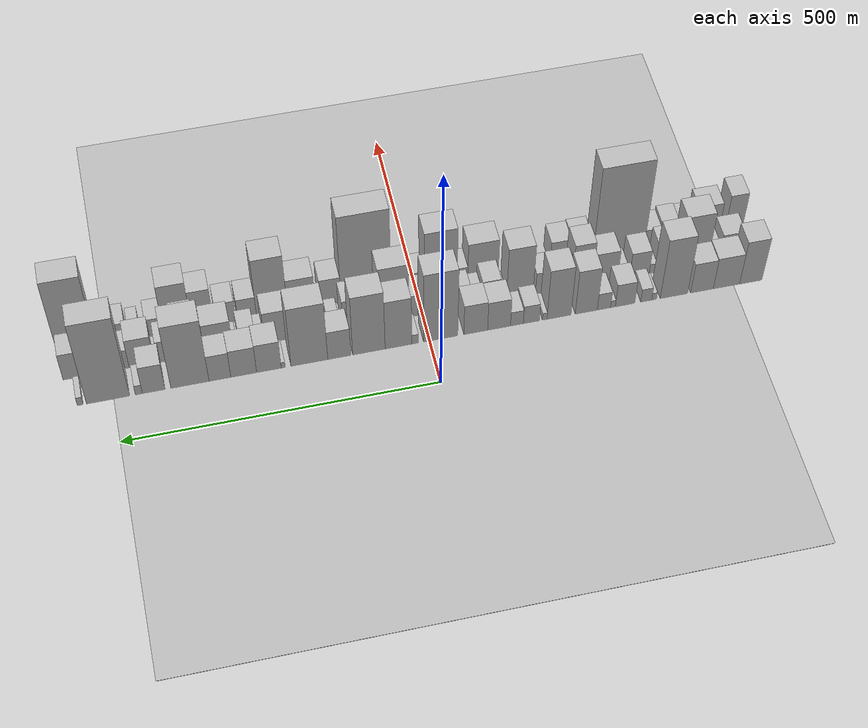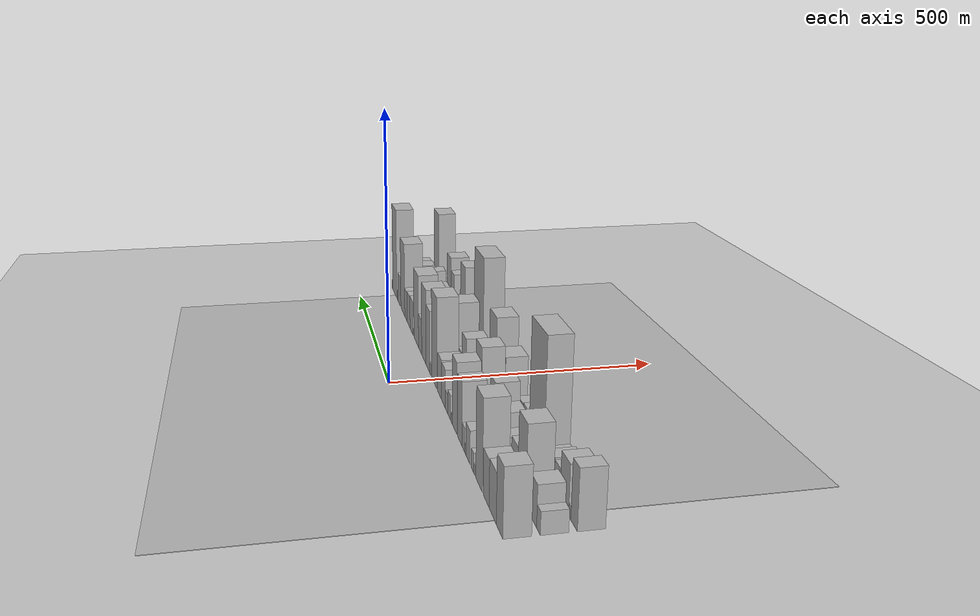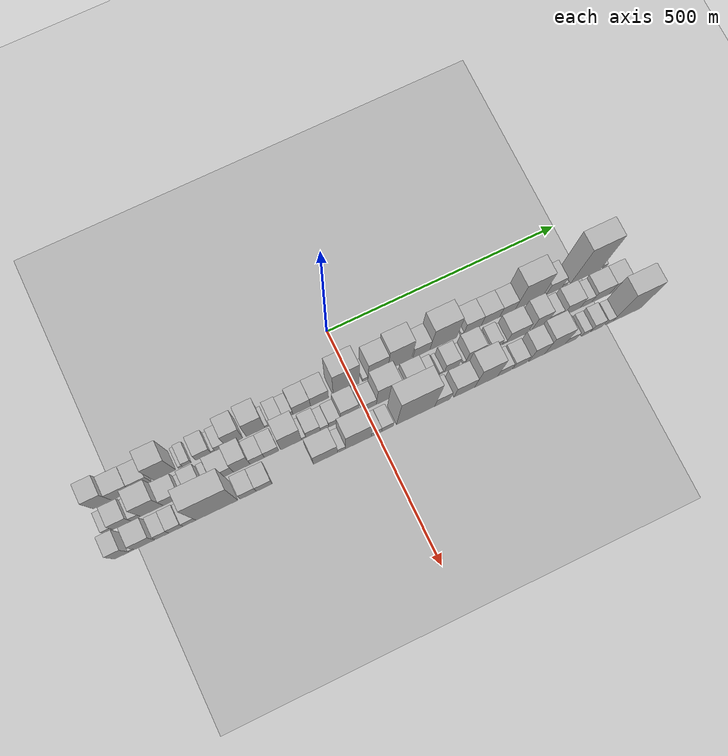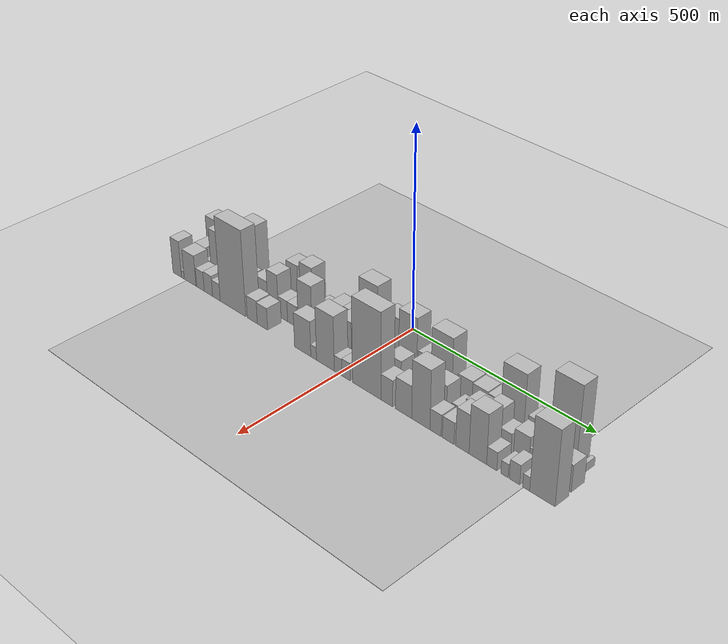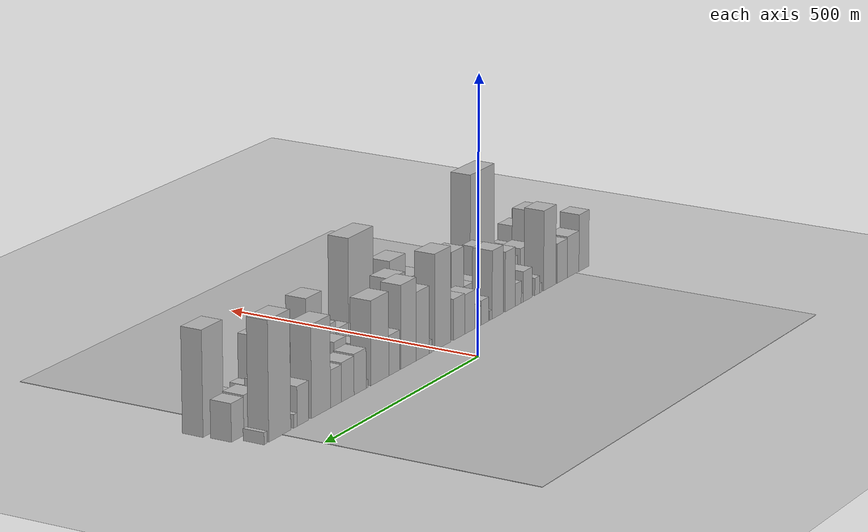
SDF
<?xml version="1.0" encoding="utf-8"?>

<sdf version="1.6">

   <world name="default">

      <gui fullscreen="0">

         <camera name="user_camera">

            <pose>-15 0 4.57585 0 0 0</pose>

            <view_controller>orbit</view_controller>

         </camera>

      </gui>

      <scene>

         <sky>

           <clouds>

             <speed>12</speed>

           </clouds>

         </sky>

         <ambient>0.4 0.4 0.4 1</ambient>

         <background>0.7 0.7 0.7 1</background>

         <shadows>1</shadows>

      </scene>

      <gravity>0 0 -9.8066</gravity>

      <magnetic_field>6e-06 2.3e-05 -4.2e-05</magnetic_field>

      <physics default="0" name="default_physics" type="ode">

         <ode>

            <solver>

               <type>quick</type>

               <iters>10</iters>

               <sor>1.0</sor>

               <use_dynamic_moi_rescaling>0</use_dynamic_moi_rescaling>

            </solver>

            <constraints>

               <cfm>0</cfm>

               <erp>0.2</erp>

               <contact_max_correcting_vel>100</contact_max_correcting_vel>

               <contact_surface_layer>0.001</contact_surface_layer>

            </constraints>

         </ode>

         <max_step_size>0.004</max_step_size>

         <real_time_factor>1</real_time_factor>

         <real_time_update_rate>250</real_time_update_rate>

      </physics>

      <light name="sun" type="directional">

         <cast_shadows>1</cast_shadows>

         <pose>0 0 10 0 0 0</pose>

         <diffuse>0.8 0.8 0.8 1</diffuse>

         <specular>0.2 0.2 0.2 1</specular>

         <attenuation>

            <range>1000</range>

            <constant>0.9</constant>

            <linear>0.01</linear>

            <quadratic>0.001</quadratic>

         </attenuation>

         <direction>-0.5 0.1 -0.9</direction>

      </light>

      <include>

         <name>ground_plane_1</name>

         <uri>model://HANNAS_ground_plane</uri>

         <pose>0 0 0  0 0 0</pose>

      </include>

      <include>

         <name>ground_plane_2</name>

         <uri>model://HANNAS_ground_plane</uri>

         <pose>100 0 0  0 0 0</pose>

      </include>

      <model name="building_1">

         <static>1</static>

         <pose frame="">100.0000 -529.0865 0 0.000000 0.000000 0.000000</pose>

         <link name="link">

            <pose frame="">0 0 54.00 0 0 0</pose>

            <collision name="collision">

               <geometry>

                  <box>

                     <size>40.0000 37.8271 108.0000</size>

                  </box>

               </geometry>

               <max_contacts>10</max_contacts>

               <surface>

                  <contact>

                     <ode/>

                  </contact>

                  <bounce/>

                  <friction>

                     <torsional>

                        <ode/>

                     </torsional>

                     <ode/>

                  </friction>

               </surface>

            </collision>

            <visual name="visual">

               <cast_shadows>0</cast_shadows>

               <geometry>

                  <box>

                     <size>40.0000 37.8271 108.0000</size>

                  </box>

               </geometry>

               <material>

                  <script>

                     <uri>model://HANNAS_wall/materials/scripts</uri>

                     <uri>model://HANNAS_wall/materials/textures</uri>

                     <name>vrc/HANNAS_wall</name>

                  </script>

               </material>

            </visual>

            <self_collide>0</self_collide>

            <enable_wind>0</enable_wind>

            <kinematic>0</kinematic>

         </link>

      </model>

      <model name="building_2">

         <static>1</static>

         <pose frame="">100.0000 -488.0078 0 0.000000 0.000000 0.000000</pose>

         <link name="link">

            <pose frame="">0 0 39.00 0 0 0</pose>

            <collision name="collision">

               <geometry>

                  <box>

                     <size>40.0000 44.3302 78.0000</size>

                  </box>

               </geometry>

               <max_contacts>10</max_contacts>

               <surface>

                  <contact>

                     <ode/>

                  </contact>

                  <bounce/>

                  <friction>

                     <torsional>

                        <ode/>

                     </torsional>

                     <ode/>

                  </friction>

               </surface>

            </collision>

            <visual name="visual">

               <cast_shadows>0</cast_shadows>

               <geometry>

                  <box>

                     <size>40.0000 44.3302 78.0000</size>

                  </box>

               </geometry>

               <material>

                  <script>

                     <uri>model://HANNAS_wall/materials/scripts</uri>

                     <uri>model://HANNAS_wall/materials/textures</uri>

                     <name>vrc/HANNAS_wall</name>

                  </script>

               </material>

            </visual>

            <self_collide>0</self_collide>

            <enable_wind>0</enable_wind>

            <kinematic>0</kinematic>

         </link>

      </model>

      <model name="building_3">

         <static>1</static>

         <pose frame="">100.0000 -446.8630 0 0.000000 0.000000 0.000000</pose>

         <link name="link">

            <pose frame="">0 0 37.50 0 0 0</pose>

            <collision name="collision">

               <geometry>

                  <box>

                     <size>40.0000 37.9594 75.0000</size>

                  </box>

               </geometry>

               <max_contacts>10</max_contacts>

               <surface>

                  <contact>

                     <ode/>

                  </contact>

                  <bounce/>

                  <friction>

                     <torsional>

                        <ode/>

                     </torsional>

                     <ode/>

                  </friction>

               </surface>

            </collision>

            <visual name="visual">

               <cast_shadows>0</cast_shadows>

               <geometry>

                  <box>

                     <size>40.0000 37.9594 75.0000</size>

                  </box>

               </geometry>

               <material>

                  <script>

                     <uri>model://HANNAS_wall/materials/scripts</uri>

                     <uri>model://HANNAS_wall/materials/textures</uri>

                     <name>vrc/HANNAS_wall</name>

                  </script>

               </material>

            </visual>

            <self_collide>0</self_collide>

            <enable_wind>0</enable_wind>

            <kinematic>0</kinematic>

         </link>

      </model>

      <model name="building_4">

         <static>1</static>

         <pose frame="">100.0000 -399.9575 0 0.000000 0.000000 0.000000</pose>

         <link name="link">

            <pose frame="">0 0 75.00 0 0 0</pose>

            <collision name="collision">

               <geometry>

                  <box>

                     <size>40.0000 45.8516 150.0000</size>

                  </box>

               </geometry>

               <max_contacts>10</max_contacts>

               <surface>

                  <contact>

                     <ode/>

                  </contact>

                  <bounce/>

                  <friction>

                     <torsional>

                        <ode/>

                     </torsional>

                     <ode/>

                  </friction>

               </surface>

            </collision>

            <visual name="visual">

               <cast_shadows>0</cast_shadows>

               <geometry>

                  <box>

                     <size>40.0000 45.8516 150.0000</size>

                  </box>

               </geometry>

               <material>

                  <script>

                     <uri>model://HANNAS_wall/materials/scripts</uri>

                     <uri>model://HANNAS_wall/materials/textures</uri>

                     <name>vrc/HANNAS_wall</name>

                  </script>

               </material>

            </visual>

            <self_collide>0</self_collide>

            <enable_wind>0</enable_wind>

            <kinematic>0</kinematic>

         </link>

      </model>

      <model name="building_5">

         <static>1</static>

         <pose frame="">100.0000 -367.0012 0 0.000000 0.000000 0.000000</pose>

         <link name="link">

            <pose frame="">0 0 9.00 0 0 0</pose>

            <collision name="collision">

               <geometry>

                  <box>

                     <size>40.0000 8.0611 18.0000</size>

                  </box>

               </geometry>

               <max_contacts>10</max_contacts>

               <surface>

                  <contact>

                     <ode/>

                  </contact>

                  <bounce/>

                  <friction>

                     <torsional>

                        <ode/>

                     </torsional>

                     <ode/>

                  </friction>

               </surface>

            </collision>

            <visual name="visual">

               <cast_shadows>0</cast_shadows>

               <geometry>

                  <box>

                     <size>40.0000 8.0611 18.0000</size>

                  </box>

               </geometry>

               <material>

                  <script>

                     <uri>model://HANNAS_wall/materials/scripts</uri>

                     <uri>model://HANNAS_wall/materials/textures</uri>

                     <name>vrc/HANNAS_wall</name>

                  </script>

               </material>

            </visual>

            <self_collide>0</self_collide>

            <enable_wind>0</enable_wind>

            <kinematic>0</kinematic>

         </link>

      </model>

      <model name="building_6">

         <static>1</static>

         <pose frame="">100.0000 -353.8324 0 0.000000 0.000000 0.000000</pose>

         <link name="link">

            <pose frame="">0 0 16.50 0 0 0</pose>

            <collision name="collision">

               <geometry>

                  <box>

                     <size>40.0000 18.2765 33.0000</size>

                  </box>

               </geometry>

               <max_contacts>10</max_contacts>

               <surface>

                  <contact>

                     <ode/>

                  </contact>

                  <bounce/>

                  <friction>

                     <torsional>

                        <ode/>

                     </torsional>

                     <ode/>

                  </friction>

               </surface>

            </collision>

            <visual name="visual">

               <cast_shadows>0</cast_shadows>

               <geometry>

                  <box>

                     <size>40.0000 18.2765 33.0000</size>

                  </box>

               </geometry>

               <material>

                  <script>

                     <uri>model://HANNAS_wall/materials/scripts</uri>

                     <uri>model://HANNAS_wall/materials/textures</uri>

                     <name>vrc/HANNAS_wall</name>

                  </script>

               </material>

            </visual>

            <self_collide>0</self_collide>

            <enable_wind>0</enable_wind>

            <kinematic>0</kinematic>

         </link>

      </model>

      <model name="building_7">

         <static>1</static>

         <pose frame="">100.0000 -318.5641 0 0.000000 0.000000 0.000000</pose>

         <link name="link">

            <pose frame="">0 0 28.50 0 0 0</pose>

            <collision name="collision">

               <geometry>

                  <box>

                     <size>40.0000 32.2601 57.0000</size>

                  </box>

               </geometry>

               <max_contacts>10</max_contacts>

               <surface>

                  <contact>

                     <ode/>

                  </contact>

                  <bounce/>

                  <friction>

                     <torsional>

                        <ode/>

                     </torsional>

                     <ode/>

                  </friction>

               </surface>

            </collision>

            <visual name="visual">

               <cast_shadows>0</cast_shadows>

               <geometry>

                  <box>

                     <size>40.0000 32.2601 57.0000</size>

                  </box>

               </geometry>

               <material>

                  <script>

                     <uri>model://HANNAS_wall/materials/scripts</uri>

                     <uri>model://HANNAS_wall/materials/textures</uri>

                     <name>vrc/HANNAS_wall</name>

                  </script>

               </material>

            </visual>

            <self_collide>0</self_collide>

            <enable_wind>0</enable_wind>

            <kinematic>0</kinematic>

         </link>

      </model>

      <model name="building_8">

         <static>1</static>

         <pose frame="">100.0000 -298.6236 0 0.000000 0.000000 0.000000</pose>

         <link name="link">

            <pose frame="">0 0 9.00 0 0 0</pose>

            <collision name="collision">

               <geometry>

                  <box>

                     <size>40.0000 7.6209 18.0000</size>

                  </box>

               </geometry>

               <max_contacts>10</max_contacts>

               <surface>

                  <contact>

                     <ode/>

                  </contact>

                  <bounce/>

                  <friction>

                     <torsional>

                        <ode/>

                     </torsional>

                     <ode/>

                  </friction>

               </surface>

            </collision>

            <visual name="visual">

               <cast_shadows>0</cast_shadows>

               <geometry>

                  <box>

                     <size>40.0000 7.6209 18.0000</size>

                  </box>

               </geometry>

               <material>

                  <script>

                     <uri>model://HANNAS_wall/materials/scripts</uri>

                     <uri>model://HANNAS_wall/materials/textures</uri>

                     <name>vrc/HANNAS_wall</name>

                  </script>

               </material>

            </visual>

            <self_collide>0</self_collide>

            <enable_wind>0</enable_wind>

            <kinematic>0</kinematic>

         </link>

      </model>

      <model name="building_9">

         <static>1</static>

         <pose frame="">100.0000 -283.7760 0 0.000000 0.000000 0.000000</pose>

         <link name="link">

            <pose frame="">0 0 21.00 0 0 0</pose>

            <collision name="collision">

               <geometry>

                  <box>

                     <size>40.0000 22.0742 42.0000</size>

                  </box>

               </geometry>

               <max_contacts>10</max_contacts>

               <surface>

                  <contact>

                     <ode/>

                  </contact>

                  <bounce/>

                  <friction>

                     <torsional>

                        <ode/>

                     </torsional>

                     <ode/>

                  </friction>

               </surface>

            </collision>

            <visual name="visual">

               <cast_shadows>0</cast_shadows>

               <geometry>

                  <box>

                     <size>40.0000 22.0742 42.0000</size>

                  </box>

               </geometry>

               <material>

                  <script>

                     <uri>model://HANNAS_wall/materials/scripts</uri>

                     <uri>model://HANNAS_wall/materials/textures</uri>

                     <name>vrc/HANNAS_wall</name>

                  </script>

               </material>

            </visual>

            <self_collide>0</self_collide>

            <enable_wind>0</enable_wind>

            <kinematic>0</kinematic>

         </link>

      </model>

      <model name="building_10">

         <static>1</static>

         <pose frame="">100.0000 -254.5363 0 0.000000 0.000000 0.000000</pose>

         <link name="link">

            <pose frame="">0 0 55.50 0 0 0</pose>

            <collision name="collision">

               <geometry>

                  <box>

                     <size>40.0000 36.4053 111.0000</size>

                  </box>

               </geometry>

               <max_contacts>10</max_contacts>

               <surface>

                  <contact>

                     <ode/>

                  </contact>

                  <bounce/>

                  <friction>

                     <torsional>

                        <ode/>

                     </torsional>

                     <ode/>

                  </friction>

               </surface>

            </collision>

            <visual name="visual">

               <cast_shadows>0</cast_shadows>

               <geometry>

                  <box>

                     <size>40.0000 36.4053 111.0000</size>

                  </box>

               </geometry>

               <material>

                  <script>

                     <uri>model://HANNAS_wall/materials/scripts</uri>

                     <uri>model://HANNAS_wall/materials/textures</uri>

                     <name>vrc/HANNAS_wall</name>

                  </script>

               </material>

            </visual>

            <self_collide>0</self_collide>

            <enable_wind>0</enable_wind>

            <kinematic>0</kinematic>

         </link>

      </model>

      <model name="building_11">

         <static>1</static>

         <pose frame="">100.0000 -209.6078 0 0.000000 0.000000 0.000000</pose>

         <link name="link">

            <pose frame="">0 0 63.00 0 0 0</pose>

            <collision name="collision">

               <geometry>

                  <box>

                     <size>40.0000 39.4516 126.0000</size>

                  </box>

               </geometry>

               <max_contacts>10</max_contacts>

               <surface>

                  <contact>

                     <ode/>

                  </contact>

                  <bounce/>

                  <friction>

                     <torsional>

                        <ode/>

                     </torsional>

                     <ode/>

                  </friction>

               </surface>

            </collision>

            <visual name="visual">

               <cast_shadows>0</cast_shadows>

               <geometry>

                  <box>

                     <size>40.0000 39.4516 126.0000</size>

                  </box>

               </geometry>

               <material>

                  <script>

                     <uri>model://HANNAS_wall/materials/scripts</uri>

                     <uri>model://HANNAS_wall/materials/textures</uri>

                     <name>vrc/HANNAS_wall</name>

                  </script>

               </material>

            </visual>

            <self_collide>0</self_collide>

            <enable_wind>0</enable_wind>

            <kinematic>0</kinematic>

         </link>

      </model>

      <model name="building_12">

         <static>1</static>

         <pose frame="">100.0000 -186.1503 0 0.000000 0.000000 0.000000</pose>

         <link name="link">

            <pose frame="">0 0 9.00 0 0 0</pose>

            <collision name="collision">

               <geometry>

                  <box>

                     <size>40.0000 7.4635 18.0000</size>

                  </box>

               </geometry>

               <max_contacts>10</max_contacts>

               <surface>

                  <contact>

                     <ode/>

                  </contact>

                  <bounce/>

                  <friction>

                     <torsional>

                        <ode/>

                     </torsional>

                     <ode/>

                  </friction>

               </surface>

            </collision>

            <visual name="visual">

               <cast_shadows>0</cast_shadows>

               <geometry>

                  <box>

                     <size>40.0000 7.4635 18.0000</size>

                  </box>

               </geometry>

               <material>

                  <script>

                     <uri>model://HANNAS_wall/materials/scripts</uri>

                     <uri>model://HANNAS_wall/materials/textures</uri>

                     <name>vrc/HANNAS_wall</name>

                  </script>

               </material>

            </visual>

            <self_collide>0</self_collide>

            <enable_wind>0</enable_wind>

            <kinematic>0</kinematic>

         </link>

      </model>

      <model name="building_13">

         <static>1</static>

         <pose frame="">100.0000 -164.3132 0 0.000000 0.000000 0.000000</pose>

         <link name="link">

            <pose frame="">0 0 22.50 0 0 0</pose>

            <collision name="collision">

               <geometry>

                  <box>

                     <size>40.0000 26.2106 45.0000</size>

                  </box>

               </geometry>

               <max_contacts>10</max_contacts>

               <surface>

                  <contact>

                     <ode/>

                  </contact>

                  <bounce/>

                  <friction>

                     <torsional>

                        <ode/>

                     </torsional>

                     <ode/>

                  </friction>

               </surface>

            </collision>

            <visual name="visual">

               <cast_shadows>0</cast_shadows>

               <geometry>

                  <box>

                     <size>40.0000 26.2106 45.0000</size>

                  </box>

               </geometry>

               <material>

                  <script>

                     <uri>model://HANNAS_wall/materials/scripts</uri>

                     <uri>model://HANNAS_wall/materials/textures</uri>

                     <name>vrc/HANNAS_wall</name>

                  </script>

               </material>

            </visual>

            <self_collide>0</self_collide>

            <enable_wind>0</enable_wind>

            <kinematic>0</kinematic>

         </link>

      </model>

      <model name="building_14">

         <static>1</static>

         <pose frame="">100.0000 -140.6801 0 0.000000 0.000000 0.000000</pose>

         <link name="link">

            <pose frame="">0 0 18.00 0 0 0</pose>

            <collision name="collision">

               <geometry>

                  <box>

                     <size>40.0000 21.0555 36.0000</size>

                  </box>

               </geometry>

               <max_contacts>10</max_contacts>

               <surface>

                  <contact>

                     <ode/>

                  </contact>

                  <bounce/>

                  <friction>

                     <torsional>

                        <ode/>

                     </torsional>

                     <ode/>

                  </friction>

               </surface>

            </collision>

            <visual name="visual">

               <cast_shadows>0</cast_shadows>

               <geometry>

                  <box>

                     <size>40.0000 21.0555 36.0000</size>

                  </box>

               </geometry>

               <material>

                  <script>

                     <uri>model://HANNAS_wall/materials/scripts</uri>

                     <uri>model://HANNAS_wall/materials/textures</uri>

                     <name>vrc/HANNAS_wall</name>

                  </script>

               </material>

            </visual>

            <self_collide>0</self_collide>

            <enable_wind>0</enable_wind>

            <kinematic>0</kinematic>

         </link>

      </model>

      <model name="building_15">

         <static>1</static>

         <pose frame="">100.0000 -111.5379 0 0.000000 0.000000 0.000000</pose>

         <link name="link">

            <pose frame="">0 0 36.00 0 0 0</pose>

            <collision name="collision">

               <geometry>

                  <box>

                     <size>40.0000 37.2290 72.0000</size>

                  </box>

               </geometry>

               <max_contacts>10</max_contacts>

               <surface>

                  <contact>

                     <ode/>

                  </contact>

                  <bounce/>

                  <friction>

                     <torsional>

                        <ode/>

                     </torsional>

                     <ode/>

                  </friction>

               </surface>

            </collision>

            <visual name="visual">

               <cast_shadows>0</cast_shadows>

               <geometry>

                  <box>

                     <size>40.0000 37.2290 72.0000</size>

                  </box>

               </geometry>

               <material>

                  <script>

                     <uri>model://HANNAS_wall/materials/scripts</uri>

                     <uri>model://HANNAS_wall/materials/textures</uri>

                     <name>vrc/HANNAS_wall</name>

                  </script>

               </material>

            </visual>

            <self_collide>0</self_collide>

            <enable_wind>0</enable_wind>

            <kinematic>0</kinematic>

         </link>

      </model>

      <model name="building_16">

         <static>1</static>

         <pose frame="">100.0000 -73.6585 0 0.000000 0.000000 0.000000</pose>

         <link name="link">

            <pose frame="">0 0 37.50 0 0 0</pose>

            <collision name="collision">

               <geometry>

                  <box>

                     <size>40.0000 38.5298 75.0000</size>

                  </box>

               </geometry>

               <max_contacts>10</max_contacts>

               <surface>

                  <contact>

                     <ode/>

                  </contact>

                  <bounce/>

                  <friction>

                     <torsional>

                        <ode/>

                     </torsional>

                     <ode/>

                  </friction>

               </surface>

            </collision>

            <visual name="visual">

               <cast_shadows>0</cast_shadows>

               <geometry>

                  <box>

                     <size>40.0000 38.5298 75.0000</size>

                  </box>

               </geometry>

               <material>

                  <script>

                     <uri>model://HANNAS_wall/materials/scripts</uri>

                     <uri>model://HANNAS_wall/materials/textures</uri>

                     <name>vrc/HANNAS_wall</name>

                  </script>

               </material>

            </visual>

            <self_collide>0</self_collide>

            <enable_wind>0</enable_wind>

            <kinematic>0</kinematic>

         </link>

      </model>

      <model name="building_17">

         <static>1</static>

         <pose frame="">100.0000 -16.7990 0 0.000000 0.000000 0.000000</pose>

         <link name="link">

            <pose frame="">0 0 87.00 0 0 0</pose>

            <collision name="collision">

               <geometry>

                  <box>

                     <size>40.0000 55.1892 174.0000</size>

                  </box>

               </geometry>

               <max_contacts>10</max_contacts>

               <surface>

                  <contact>

                     <ode/>

                  </contact>

                  <bounce/>

                  <friction>

                     <torsional>

                        <ode/>

                     </torsional>

                     <ode/>

                  </friction>

               </surface>

            </collision>

            <visual name="visual">

               <cast_shadows>0</cast_shadows>

               <geometry>

                  <box>

                     <size>40.0000 55.1892 174.0000</size>

                  </box>

               </geometry>

               <material>

                  <script>

                     <uri>model://HANNAS_wall/materials/scripts</uri>

                     <uri>model://HANNAS_wall/materials/textures</uri>

                     <name>vrc/HANNAS_wall</name>

                  </script>

               </material>

            </visual>

            <self_collide>0</self_collide>

            <enable_wind>0</enable_wind>

            <kinematic>0</kinematic>

         </link>

      </model>

      <model name="building_18">

         <static>1</static>

         <pose frame="">100.0000 24.2222 0 0.000000 0.000000 0.000000</pose>

         <link name="link">

            <pose frame="">0 0 12.00 0 0 0</pose>

            <collision name="collision">

               <geometry>

                  <box>

                     <size>40.0000 10.8533 24.0000</size>

                  </box>

               </geometry>

               <max_contacts>10</max_contacts>

               <surface>

                  <contact>

                     <ode/>

                  </contact>

                  <bounce/>

                  <friction>

                     <torsional>

                        <ode/>

                     </torsional>

                     <ode/>

                  </friction>

               </surface>

            </collision>

            <visual name="visual">

               <cast_shadows>0</cast_shadows>

               <geometry>

                  <box>

                     <size>40.0000 10.8533 24.0000</size>

                  </box>

               </geometry>

               <material>

                  <script>

                     <uri>model://HANNAS_wall/materials/scripts</uri>

                     <uri>model://HANNAS_wall/materials/textures</uri>

                     <name>vrc/HANNAS_wall</name>

                  </script>

               </material>

            </visual>

            <self_collide>0</self_collide>

            <enable_wind>0</enable_wind>

            <kinematic>0</kinematic>

         </link>

      </model>

      <model name="building_19">

         <static>1</static>

         <pose frame="">100.0000 51.1228 0 0.000000 0.000000 0.000000</pose>

         <link name="link">

            <pose frame="">0 0 61.50 0 0 0</pose>

            <collision name="collision">

               <geometry>

                  <box>

                     <size>40.0000 42.9478 123.0000</size>

                  </box>

               </geometry>

               <max_contacts>10</max_contacts>

               <surface>

                  <contact>

                     <ode/>

                  </contact>

                  <bounce/>

                  <friction>

                     <torsional>

                        <ode/>

                     </torsional>

                     <ode/>

                  </friction>

               </surface>

            </collision>

            <visual name="visual">

               <cast_shadows>0</cast_shadows>

               <geometry>

                  <box>

                     <size>40.0000 42.9478 123.0000</size>

                  </box>

               </geometry>

               <material>

                  <script>

                     <uri>model://HANNAS_wall/materials/scripts</uri>

                     <uri>model://HANNAS_wall/materials/textures</uri>

                     <name>vrc/HANNAS_wall</name>

                  </script>

               </material>

            </visual>

            <self_collide>0</self_collide>

            <enable_wind>0</enable_wind>

            <kinematic>0</kinematic>

         </link>

      </model>

      <model name="building_20">

         <static>1</static>

         <pose frame="">100.0000 98.5554 0 0.000000 0.000000 0.000000</pose>

         <link name="link">

            <pose frame="">0 0 75.00 0 0 0</pose>

            <collision name="collision">

               <geometry>

                  <box>

                     <size>40.0000 51.9175 150.0000</size>

                  </box>

               </geometry>

               <max_contacts>10</max_contacts>

               <surface>

                  <contact>

                     <ode/>

                  </contact>

                  <bounce/>

                  <friction>

                     <torsional>

                        <ode/>

                     </torsional>

                     <ode/>

                  </friction>

               </surface>

            </collision>

            <visual name="visual">

               <cast_shadows>0</cast_shadows>

               <geometry>

                  <box>

                     <size>40.0000 51.9175 150.0000</size>

                  </box>

               </geometry>

               <material>

                  <script>

                     <uri>model://HANNAS_wall/materials/scripts</uri>

                     <uri>model://HANNAS_wall/materials/textures</uri>

                     <name>vrc/HANNAS_wall</name>

                  </script>

               </material>

            </visual>

            <self_collide>0</self_collide>

            <enable_wind>0</enable_wind>

            <kinematic>0</kinematic>

         </link>

      </model>

      <model name="building_21">

         <static>1</static>

         <pose frame="">100.0000 145.8838 0 0.000000 0.000000 0.000000</pose>

         <link name="link">

            <pose frame="">0 0 36.00 0 0 0</pose>

            <collision name="collision">

               <geometry>

                  <box>

                     <size>40.0000 36.7392 72.0000</size>

                  </box>

               </geometry>

               <max_contacts>10</max_contacts>

               <surface>

                  <contact>

                     <ode/>

                  </contact>

                  <bounce/>

                  <friction>

                     <torsional>

                        <ode/>

                     </torsional>

                     <ode/>

                  </friction>

               </surface>

            </collision>

            <visual name="visual">

               <cast_shadows>0</cast_shadows>

               <geometry>

                  <box>

                     <size>40.0000 36.7392 72.0000</size>

                  </box>

               </geometry>

               <material>

                  <script>

                     <uri>model://HANNAS_wall/materials/scripts</uri>

                     <uri>model://HANNAS_wall/materials/textures</uri>

                     <name>vrc/HANNAS_wall</name>

                  </script>

               </material>

            </visual>

            <self_collide>0</self_collide>

            <enable_wind>0</enable_wind>

            <kinematic>0</kinematic>

         </link>

      </model>

      <model name="building_22">

         <static>1</static>

         <pose frame="">100.0000 193.4489 0 0.000000 0.000000 0.000000</pose>

         <link name="link">

            <pose frame="">0 0 75.00 0 0 0</pose>

            <collision name="collision">

               <geometry>

                  <box>

                     <size>40.0000 58.3910 150.0000</size>

                  </box>

               </geometry>

               <max_contacts>10</max_contacts>

               <surface>

                  <contact>

                     <ode/>

                  </contact>

                  <bounce/>

                  <friction>

                     <torsional>

                        <ode/>

                     </torsional>

                     <ode/>

                  </friction>

               </surface>

            </collision>

            <visual name="visual">

               <cast_shadows>0</cast_shadows>

               <geometry>

                  <box>

                     <size>40.0000 58.3910 150.0000</size>

                  </box>

               </geometry>

               <material>

                  <script>

                     <uri>model://HANNAS_wall/materials/scripts</uri>

                     <uri>model://HANNAS_wall/materials/textures</uri>

                     <name>vrc/HANNAS_wall</name>

                  </script>

               </material>

            </visual>

            <self_collide>0</self_collide>

            <enable_wind>0</enable_wind>

            <kinematic>0</kinematic>

         </link>

      </model>

      <model name="building_23">

         <static>1</static>

         <pose frame="">100.0000 234.8274 0 0.000000 0.000000 0.000000</pose>

         <link name="link">

            <pose frame="">0 0 7.50 0 0 0</pose>

            <collision name="collision">

               <geometry>

                  <box>

                     <size>40.0000 6.3659 15.0000</size>

                  </box>

               </geometry>

               <max_contacts>10</max_contacts>

               <surface>

                  <contact>

                     <ode/>

                  </contact>

                  <bounce/>

                  <friction>

                     <torsional>

                        <ode/>

                     </torsional>

                     <ode/>

                  </friction>

               </surface>

            </collision>

            <visual name="visual">

               <cast_shadows>0</cast_shadows>

               <geometry>

                  <box>

                     <size>40.0000 6.3659 15.0000</size>

                  </box>

               </geometry>

               <material>

                  <script>

                     <uri>model://HANNAS_wall/materials/scripts</uri>

                     <uri>model://HANNAS_wall/materials/textures</uri>

                     <name>vrc/HANNAS_wall</name>

                  </script>

               </material>

            </visual>

            <self_collide>0</self_collide>

            <enable_wind>0</enable_wind>

            <kinematic>0</kinematic>

         </link>

      </model>

      <model name="building_24">

         <static>1</static>

         <pose frame="">100.0000 257.4116 0 0.000000 0.000000 0.000000</pose>

         <link name="link">

            <pose frame="">0 0 36.00 0 0 0</pose>

            <collision name="collision">

               <geometry>

                  <box>

                     <size>40.0000 38.8025 72.0000</size>

                  </box>

               </geometry>

               <max_contacts>10</max_contacts>

               <surface>

                  <contact>

                     <ode/>

                  </contact>

                  <bounce/>

                  <friction>

                     <torsional>

                        <ode/>

                     </torsional>

                     <ode/>

                  </friction>

               </surface>

            </collision>

            <visual name="visual">

               <cast_shadows>0</cast_shadows>

               <geometry>

                  <box>

                     <size>40.0000 38.8025 72.0000</size>

                  </box>

               </geometry>

               <material>

                  <script>

                     <uri>model://HANNAS_wall/materials/scripts</uri>

                     <uri>model://HANNAS_wall/materials/textures</uri>

                     <name>vrc/HANNAS_wall</name>

                  </script>

               </material>

            </visual>

            <self_collide>0</self_collide>

            <enable_wind>0</enable_wind>

            <kinematic>0</kinematic>

         </link>

      </model>

      <model name="building_25">

         <static>1</static>

         <pose frame="">100.0000 297.0847 0 0.000000 0.000000 0.000000</pose>

         <link name="link">

            <pose frame="">0 0 34.50 0 0 0</pose>

            <collision name="collision">

               <geometry>

                  <box>

                     <size>40.0000 40.5437 69.0000</size>

                  </box>

               </geometry>

               <max_contacts>10</max_contacts>

               <surface>

                  <contact>

                     <ode/>

                  </contact>

                  <bounce/>

                  <friction>

                     <torsional>

                        <ode/>

                     </torsional>

                     <ode/>

                  </friction>

               </surface>

            </collision>

            <visual name="visual">

               <cast_shadows>0</cast_shadows>

               <geometry>

                  <box>

                     <size>40.0000 40.5437 69.0000</size>

                  </box>

               </geometry>

               <material>

                  <script>

                     <uri>model://HANNAS_wall/materials/scripts</uri>

                     <uri>model://HANNAS_wall/materials/textures</uri>

                     <name>vrc/HANNAS_wall</name>

                  </script>

               </material>

            </visual>

            <self_collide>0</self_collide>

            <enable_wind>0</enable_wind>

            <kinematic>0</kinematic>

         </link>

      </model>

      <model name="building_26">

         <static>1</static>

         <pose frame="">100.0000 334.4643 0 0.000000 0.000000 0.000000</pose>

         <link name="link">

            <pose frame="">0 0 33.00 0 0 0</pose>

            <collision name="collision">

               <geometry>

                  <box>

                     <size>40.0000 34.2156 66.0000</size>

                  </box>

               </geometry>

               <max_contacts>10</max_contacts>

               <surface>

                  <contact>

                     <ode/>

                  </contact>

                  <bounce/>

                  <friction>

                     <torsional>

                        <ode/>

                     </torsional>

                     <ode/>

                  </friction>

               </surface>

            </collision>

            <visual name="visual">

               <cast_shadows>0</cast_shadows>

               <geometry>

                  <box>

                     <size>40.0000 34.2156 66.0000</size>

                  </box>

               </geometry>

               <material>

                  <script>

                     <uri>model://HANNAS_wall/materials/scripts</uri>

                     <uri>model://HANNAS_wall/materials/textures</uri>

                     <name>vrc/HANNAS_wall</name>

                  </script>

               </material>

            </visual>

            <self_collide>0</self_collide>

            <enable_wind>0</enable_wind>

            <kinematic>0</kinematic>

         </link>

      </model>

      <model name="building_27">

         <static>1</static>

         <pose frame="">100.0000 381.3881 0 0.000000 0.000000 0.000000</pose>

         <link name="link">

            <pose frame="">0 0 81.00 0 0 0</pose>

            <collision name="collision">

               <geometry>

                  <box>

                     <size>40.0000 59.6318 162.0000</size>

                  </box>

               </geometry>

               <max_contacts>10</max_contacts>

               <surface>

                  <contact>

                     <ode/>

                  </contact>

                  <bounce/>

                  <friction>

                     <torsional>

                        <ode/>

                     </torsional>

                     <ode/>

                  </friction>

               </surface>

            </collision>

            <visual name="visual">

               <cast_shadows>0</cast_shadows>

               <geometry>

                  <box>

                     <size>40.0000 59.6318 162.0000</size>

                  </box>

               </geometry>

               <material>

                  <script>

                     <uri>model://HANNAS_wall/materials/scripts</uri>

                     <uri>model://HANNAS_wall/materials/textures</uri>

                     <name>vrc/HANNAS_wall</name>

                  </script>

               </material>

            </visual>

            <self_collide>0</self_collide>

            <enable_wind>0</enable_wind>

            <kinematic>0</kinematic>

         </link>

      </model>

      <model name="building_28">

         <static>1</static>

         <pose frame="">100.0000 437.8209 0 0.000000 0.000000 0.000000</pose>

         <link name="link">

            <pose frame="">0 0 34.50 0 0 0</pose>

            <collision name="collision">

               <geometry>

                  <box>

                     <size>40.0000 35.2339 69.0000</size>

                  </box>

               </geometry>

               <max_contacts>10</max_contacts>

               <surface>

                  <contact>

                     <ode/>

                  </contact>

                  <bounce/>

                  <friction>

                     <torsional>

                        <ode/>

                     </torsional>

                     <ode/>

                  </friction>

               </surface>

            </collision>

            <visual name="visual">

               <cast_shadows>0</cast_shadows>

               <geometry>

                  <box>

                     <size>40.0000 35.2339 69.0000</size>

                  </box>

               </geometry>

               <material>

                  <script>

                     <uri>model://HANNAS_wall/materials/scripts</uri>

                     <uri>model://HANNAS_wall/materials/textures</uri>

                     <name>vrc/HANNAS_wall</name>

                  </script>

               </material>

            </visual>

            <self_collide>0</self_collide>

            <enable_wind>0</enable_wind>

            <kinematic>0</kinematic>

         </link>

      </model>

      <model name="building_29">

         <static>1</static>

         <pose frame="">100.0000 460.8552 0 0.000000 0.000000 0.000000</pose>

         <link name="link">

            <pose frame="">0 0 12.00 0 0 0</pose>

            <collision name="collision">

               <geometry>

                  <box>

                     <size>40.0000 10.8346 24.0000</size>

                  </box>

               </geometry>

               <max_contacts>10</max_contacts>

               <surface>

                  <contact>

                     <ode/>

                  </contact>

                  <bounce/>

                  <friction>

                     <torsional>

                        <ode/>

                     </torsional>

                     <ode/>

                  </friction>

               </surface>

            </collision>

            <visual name="visual">

               <cast_shadows>0</cast_shadows>

               <geometry>

                  <box>

                     <size>40.0000 10.8346 24.0000</size>

                  </box>

               </geometry>

               <material>

                  <script>

                     <uri>model://HANNAS_wall/materials/scripts</uri>

                     <uri>model://HANNAS_wall/materials/textures</uri>

                     <name>vrc/HANNAS_wall</name>

                  </script>

               </material>

            </visual>

            <self_collide>0</self_collide>

            <enable_wind>0</enable_wind>

            <kinematic>0</kinematic>

         </link>

      </model>

      <model name="building_30">

         <static>1</static>

         <pose frame="">100.0000 508.5867 0 0.000000 0.000000 0.000000</pose>

         <link name="link">

            <pose frame="">0 0 103.50 0 0 0</pose>

            <collision name="collision">

               <geometry>

                  <box>

                     <size>40.0000 66.6283 207.0000</size>

                  </box>

               </geometry>

               <max_contacts>10</max_contacts>

               <surface>

                  <contact>

                     <ode/>

                  </contact>

                  <bounce/>

                  <friction>

                     <torsional>

                        <ode/>

                     </torsional>

                     <ode/>

                  </friction>

               </surface>

            </collision>

            <visual name="visual">

               <cast_shadows>0</cast_shadows>

               <geometry>

                  <box>

                     <size>40.0000 66.6283 207.0000</size>

                  </box>

               </geometry>

               <material>

                  <script>

                     <uri>model://HANNAS_wall/materials/scripts</uri>

                     <uri>model://HANNAS_wall/materials/textures</uri>

                     <name>vrc/HANNAS_wall</name>

                  </script>

               </material>

            </visual>

            <self_collide>0</self_collide>

            <enable_wind>0</enable_wind>

            <kinematic>0</kinematic>

         </link>

      </model>

      <model name="building_31">

         <static>1</static>

         <pose frame="">100.0000 551.4494 0 0.000000 0.000000 0.000000</pose>

         <link name="link">

            <pose frame="">0 0 10.50 0 0 0</pose>

            <collision name="collision">

               <geometry>

                  <box>

                     <size>40.0000 9.0972 21.0000</size>

                  </box>

               </geometry>

               <max_contacts>10</max_contacts>

               <surface>

                  <contact>

                     <ode/>

                  </contact>

                  <bounce/>

                  <friction>

                     <torsional>

                        <ode/>

                     </torsional>

                     <ode/>

                  </friction>

               </surface>

            </collision>

            <visual name="visual">

               <cast_shadows>0</cast_shadows>

               <geometry>

                  <box>

                     <size>40.0000 9.0972 21.0000</size>

                  </box>

               </geometry>

               <material>

                  <script>

                     <uri>model://HANNAS_wall/materials/scripts</uri>

                     <uri>model://HANNAS_wall/materials/textures</uri>

                     <name>vrc/HANNAS_wall</name>

                  </script>

               </material>

            </visual>

            <self_collide>0</self_collide>

            <enable_wind>0</enable_wind>

            <kinematic>0</kinematic>

         </link>

      </model>

      <model name="building_32">

         <static>1</static>

         <pose frame="">152.0000 -538.5925 0 0.000000 0.000000 0.000000</pose>

         <link name="link">

            <pose frame="">0 0 18.00 0 0 0</pose>

            <collision name="collision">

               <geometry>

                  <box>

                     <size>40.0000 18.8149 36.0000</size>

                  </box>

               </geometry>

               <max_contacts>10</max_contacts>

               <surface>

                  <contact>

                     <ode/>

                  </contact>

                  <bounce/>

                  <friction>

                     <torsional>

                        <ode/>

                     </torsional>

                     <ode/>

                  </friction>

               </surface>

            </collision>

            <visual name="visual">

               <cast_shadows>0</cast_shadows>

               <geometry>

                  <box>

                     <size>40.0000 18.8149 36.0000</size>

                  </box>

               </geometry>

               <material>

                  <script>

                     <uri>model://HANNAS_wall/materials/scripts</uri>

                     <uri>model://HANNAS_wall/materials/textures</uri>

                     <name>vrc/HANNAS_wall</name>

                  </script>

               </material>

            </visual>

            <self_collide>0</self_collide>

            <enable_wind>0</enable_wind>

            <kinematic>0</kinematic>

         </link>

      </model>

      <model name="building_33">

         <static>1</static>

         <pose frame="">152.0000 -510.6719 0 0.000000 0.000000 0.000000</pose>

         <link name="link">

            <pose frame="">0 0 33.00 0 0 0</pose>

            <collision name="collision">

               <geometry>

                  <box>

                     <size>40.0000 37.0262 66.0000</size>

                  </box>

               </geometry>

               <max_contacts>10</max_contacts>

               <surface>

                  <contact>

                     <ode/>

                  </contact>

                  <bounce/>

                  <friction>

                     <torsional>

                        <ode/>

                     </torsional>

                     <ode/>

                  </friction>

               </surface>

            </collision>

            <visual name="visual">

               <cast_shadows>0</cast_shadows>

               <geometry>

                  <box>

                     <size>40.0000 37.0262 66.0000</size>

                  </box>

               </geometry>

               <material>

                  <script>

                     <uri>model://HANNAS_wall/materials/scripts</uri>

                     <uri>model://HANNAS_wall/materials/textures</uri>

                     <name>vrc/HANNAS_wall</name>

                  </script>

               </material>

            </visual>

            <self_collide>0</self_collide>

            <enable_wind>0</enable_wind>

            <kinematic>0</kinematic>

         </link>

      </model>

      <model name="building_34">

         <static>1</static>

         <pose frame="">152.0000 -482.3743 0 0.000000 0.000000 0.000000</pose>

         <link name="link">

            <pose frame="">0 0 19.50 0 0 0</pose>

            <collision name="collision">

               <geometry>

                  <box>

                     <size>40.0000 19.5690 39.0000</size>

                  </box>

               </geometry>

               <max_contacts>10</max_contacts>

               <surface>

                  <contact>

                     <ode/>

                  </contact>

                  <bounce/>

                  <friction>

                     <torsional>

                        <ode/>

                     </torsional>

                     <ode/>

                  </friction>

               </surface>

            </collision>

            <visual name="visual">

               <cast_shadows>0</cast_shadows>

               <geometry>

                  <box>

                     <size>40.0000 19.5690 39.0000</size>

                  </box>

               </geometry>

               <material>

                  <script>

                     <uri>model://HANNAS_wall/materials/scripts</uri>

                     <uri>model://HANNAS_wall/materials/textures</uri>

                     <name>vrc/HANNAS_wall</name>

                  </script>

               </material>

            </visual>

            <self_collide>0</self_collide>

            <enable_wind>0</enable_wind>

            <kinematic>0</kinematic>

         </link>

      </model>

      <model name="building_35">

         <static>1</static>

         <pose frame="">152.0000 -449.0879 0 0.000000 0.000000 0.000000</pose>

         <link name="link">

            <pose frame="">0 0 64.50 0 0 0</pose>

            <collision name="collision">

               <geometry>

                  <box>

                     <size>40.0000 47.0038 129.0000</size>

                  </box>

               </geometry>

               <max_contacts>10</max_contacts>

               <surface>

                  <contact>

                     <ode/>

                  </contact>

                  <bounce/>

                  <friction>

                     <torsional>

                        <ode/>

                     </torsional>

                     <ode/>

                  </friction>

               </surface>

            </collision>

            <visual name="visual">

               <cast_shadows>0</cast_shadows>

               <geometry>

                  <box>

                     <size>40.0000 47.0038 129.0000</size>

                  </box>

               </geometry>

               <material>

                  <script>

                     <uri>model://HANNAS_wall/materials/scripts</uri>

                     <uri>model://HANNAS_wall/materials/textures</uri>

                     <name>vrc/HANNAS_wall</name>

                  </script>

               </material>

            </visual>

            <self_collide>0</self_collide>

            <enable_wind>0</enable_wind>

            <kinematic>0</kinematic>

         </link>

      </model>

      <model name="building_36">

         <static>1</static>

         <pose frame="">152.0000 -405.4987 0 0.000000 0.000000 0.000000</pose>

         <link name="link">

            <pose frame="">0 0 34.50 0 0 0</pose>

            <collision name="collision">

               <geometry>

                  <box>

                     <size>40.0000 40.1747 69.0000</size>

                  </box>

               </geometry>

               <max_contacts>10</max_contacts>

               <surface>

                  <contact>

                     <ode/>

                  </contact>

                  <bounce/>

                  <friction>

                     <torsional>

                        <ode/>

                     </torsional>

                     <ode/>

                  </friction>

               </surface>

            </collision>

            <visual name="visual">

               <cast_shadows>0</cast_shadows>

               <geometry>

                  <box>

                     <size>40.0000 40.1747 69.0000</size>

                  </box>

               </geometry>

               <material>

                  <script>

                     <uri>model://HANNAS_wall/materials/scripts</uri>

                     <uri>model://HANNAS_wall/materials/textures</uri>

                     <name>vrc/HANNAS_wall</name>

                  </script>

               </material>

            </visual>

            <self_collide>0</self_collide>

            <enable_wind>0</enable_wind>

            <kinematic>0</kinematic>

         </link>

      </model>

      <model name="building_37">

         <static>1</static>

         <pose frame="">152.0000 -379.8139 0 0.000000 0.000000 0.000000</pose>

         <link name="link">

            <pose frame="">0 0 12.00 0 0 0</pose>

            <collision name="collision">

               <geometry>

                  <box>

                     <size>40.0000 11.1949 24.0000</size>

                  </box>

               </geometry>

               <max_contacts>10</max_contacts>

               <surface>

                  <contact>

                     <ode/>

                  </contact>

                  <bounce/>

                  <friction>

                     <torsional>

                        <ode/>

                     </torsional>

                     <ode/>

                  </friction>

               </surface>

            </collision>

            <visual name="visual">

               <cast_shadows>0</cast_shadows>

               <geometry>

                  <box>

                     <size>40.0000 11.1949 24.0000</size>

                  </box>

               </geometry>

               <material>

                  <script>

                     <uri>model://HANNAS_wall/materials/scripts</uri>

                     <uri>model://HANNAS_wall/materials/textures</uri>

                     <name>vrc/HANNAS_wall</name>

                  </script>

               </material>

            </visual>

            <self_collide>0</self_collide>

            <enable_wind>0</enable_wind>

            <kinematic>0</kinematic>

         </link>

      </model>

      <model name="building_38">

         <static>1</static>

         <pose frame="">152.0000 -357.7934 0 0.000000 0.000000 0.000000</pose>

         <link name="link">

            <pose frame="">0 0 30.00 0 0 0</pose>

            <collision name="collision">

               <geometry>

                  <box>

                     <size>40.0000 32.8461 60.0000</size>

                  </box>

               </geometry>

               <max_contacts>10</max_contacts>

               <surface>

                  <contact>

                     <ode/>

                  </contact>

                  <bounce/>

                  <friction>

                     <torsional>

                        <ode/>

                     </torsional>

                     <ode/>

                  </friction>

               </surface>

            </collision>

            <visual name="visual">

               <cast_shadows>0</cast_shadows>

               <geometry>

                  <box>

                     <size>40.0000 32.8461 60.0000</size>

                  </box>

               </geometry>

               <material>

                  <script>

                     <uri>model://HANNAS_wall/materials/scripts</uri>

                     <uri>model://HANNAS_wall/materials/textures</uri>

                     <name>vrc/HANNAS_wall</name>

                  </script>

               </material>

            </visual>

            <self_collide>0</self_collide>

            <enable_wind>0</enable_wind>

            <kinematic>0</kinematic>

         </link>

      </model>

      <model name="building_39">

         <static>1</static>

         <pose frame="">152.0000 -331.6220 0 0.000000 0.000000 0.000000</pose>

         <link name="link">

            <pose frame="">0 0 13.50 0 0 0</pose>

            <collision name="collision">

               <geometry>

                  <box>

                     <size>40.0000 13.4967 27.0000</size>

                  </box>

               </geometry>

               <max_contacts>10</max_contacts>

               <surface>

                  <contact>

                     <ode/>

                  </contact>

                  <bounce/>

                  <friction>

                     <torsional>

                        <ode/>

                     </torsional>

                     <ode/>

                  </friction>

               </surface>

            </collision>

            <visual name="visual">

               <cast_shadows>0</cast_shadows>

               <geometry>

                  <box>

                     <size>40.0000 13.4967 27.0000</size>

                  </box>

               </geometry>

               <material>

                  <script>

                     <uri>model://HANNAS_wall/materials/scripts</uri>

                     <uri>model://HANNAS_wall/materials/textures</uri>

                     <name>vrc/HANNAS_wall</name>

                  </script>

               </material>

            </visual>

            <self_collide>0</self_collide>

            <enable_wind>0</enable_wind>

            <kinematic>0</kinematic>

         </link>

      </model>

      <model name="building_40">

         <static>1</static>

         <pose frame="">152.0000 -300.0251 0 0.000000 0.000000 0.000000</pose>

         <link name="link">

            <pose frame="">0 0 37.50 0 0 0</pose>

            <collision name="collision">

               <geometry>

                  <box>

                     <size>40.0000 41.6972 75.0000</size>

                  </box>

               </geometry>

               <max_contacts>10</max_contacts>

               <surface>

                  <contact>

                     <ode/>

                  </contact>

                  <bounce/>

                  <friction>

                     <torsional>

                        <ode/>

                     </torsional>

                     <ode/>

                  </friction>

               </surface>

            </collision>

            <visual name="visual">

               <cast_shadows>0</cast_shadows>

               <geometry>

                  <box>

                     <size>40.0000 41.6972 75.0000</size>

                  </box>

               </geometry>

               <material>

                  <script>

                     <uri>model://HANNAS_wall/materials/scripts</uri>

                     <uri>model://HANNAS_wall/materials/textures</uri>

                     <name>vrc/HANNAS_wall</name>

                  </script>

               </material>

            </visual>

            <self_collide>0</self_collide>

            <enable_wind>0</enable_wind>

            <kinematic>0</kinematic>

         </link>

      </model>

      <model name="building_41">

         <static>1</static>

         <pose frame="">152.0000 -261.8539 0 0.000000 0.000000 0.000000</pose>

         <link name="link">

            <pose frame="">0 0 54.00 0 0 0</pose>

            <collision name="collision">

               <geometry>

                  <box>

                     <size>40.0000 34.6451 108.0000</size>

                  </box>

               </geometry>

               <max_contacts>10</max_contacts>

               <surface>

                  <contact>

                     <ode/>

                  </contact>

                  <bounce/>

                  <friction>

                     <torsional>

                        <ode/>

                     </torsional>

                     <ode/>

                  </friction>

               </surface>

            </collision>

            <visual name="visual">

               <cast_shadows>0</cast_shadows>

               <geometry>

                  <box>

                     <size>40.0000 34.6451 108.0000</size>

                  </box>

               </geometry>

               <material>

                  <script>

                     <uri>model://HANNAS_wall/materials/scripts</uri>

                     <uri>model://HANNAS_wall/materials/textures</uri>

                     <name>vrc/HANNAS_wall</name>

                  </script>

               </material>

            </visual>

            <self_collide>0</self_collide>

            <enable_wind>0</enable_wind>

            <kinematic>0</kinematic>

         </link>

      </model>

      <model name="building_42">

         <static>1</static>

         <pose frame="">152.0000 -229.7221 0 0.000000 0.000000 0.000000</pose>

         <link name="link">

            <pose frame="">0 0 27.00 0 0 0</pose>

            <collision name="collision">

               <geometry>

                  <box>

                     <size>40.0000 29.6186 54.0000</size>

                  </box>

               </geometry>

               <max_contacts>10</max_contacts>

               <surface>

                  <contact>

                     <ode/>

                  </contact>

                  <bounce/>

                  <friction>

                     <torsional>

                        <ode/>

                     </torsional>

                     <ode/>

                  </friction>

               </surface>

            </collision>

            <visual name="visual">

               <cast_shadows>0</cast_shadows>

               <geometry>

                  <box>

                     <size>40.0000 29.6186 54.0000</size>

                  </box>

               </geometry>

               <material>

                  <script>

                     <uri>model://HANNAS_wall/materials/scripts</uri>

                     <uri>model://HANNAS_wall/materials/textures</uri>

                     <name>vrc/HANNAS_wall</name>

                  </script>

               </material>

            </visual>

            <self_collide>0</self_collide>

            <enable_wind>0</enable_wind>

            <kinematic>0</kinematic>

         </link>

      </model>

      <model name="building_43">

         <static>1</static>

         <pose frame="">152.0000 -199.6353 0 0.000000 0.000000 0.000000</pose>

         <link name="link">

            <pose frame="">0 0 27.00 0 0 0</pose>

            <collision name="collision">

               <geometry>

                  <box>

                     <size>40.0000 30.5549 54.0000</size>

                  </box>

               </geometry>

               <max_contacts>10</max_contacts>

               <surface>

                  <contact>

                     <ode/>

                  </contact>

                  <bounce/>

                  <friction>

                     <torsional>

                        <ode/>

                     </torsional>

                     <ode/>

                  </friction>

               </surface>

            </collision>

            <visual name="visual">

               <cast_shadows>0</cast_shadows>

               <geometry>

                  <box>

                     <size>40.0000 30.5549 54.0000</size>

                  </box>

               </geometry>

               <material>

                  <script>

                     <uri>model://HANNAS_wall/materials/scripts</uri>

                     <uri>model://HANNAS_wall/materials/textures</uri>

                     <name>vrc/HANNAS_wall</name>

                  </script>

               </material>

            </visual>

            <self_collide>0</self_collide>

            <enable_wind>0</enable_wind>

            <kinematic>0</kinematic>

         </link>

      </model>

      <model name="building_44">

         <static>1</static>

         <pose frame="">152.0000 -158.4190 0 0.000000 0.000000 0.000000</pose>

         <link name="link">

            <pose frame="">0 0 64.50 0 0 0</pose>

            <collision name="collision">

               <geometry>

                  <box>

                     <size>40.0000 43.8778 129.0000</size>

                  </box>

               </geometry>

               <max_contacts>10</max_contacts>

               <surface>

                  <contact>

                     <ode/>

                  </contact>

                  <bounce/>

                  <friction>

                     <torsional>

                        <ode/>

                     </torsional>

                     <ode/>

                  </friction>

               </surface>

            </collision>

            <visual name="visual">

               <cast_shadows>0</cast_shadows>

               <geometry>

                  <box>

                     <size>40.0000 43.8778 129.0000</size>

                  </box>

               </geometry>

               <material>

                  <script>

                     <uri>model://HANNAS_wall/materials/scripts</uri>

                     <uri>model://HANNAS_wall/materials/textures</uri>

                     <name>vrc/HANNAS_wall</name>

                  </script>

               </material>

            </visual>

            <self_collide>0</self_collide>

            <enable_wind>0</enable_wind>

            <kinematic>0</kinematic>

         </link>

      </model>

      <model name="building_45">

         <static>1</static>

         <pose frame="">152.0000 -131.8119 0 0.000000 0.000000 0.000000</pose>

         <link name="link">

            <pose frame="">0 0 10.50 0 0 0</pose>

            <collision name="collision">

               <geometry>

                  <box>

                     <size>40.0000 9.3364 21.0000</size>

                  </box>

               </geometry>

               <max_contacts>10</max_contacts>

               <surface>

                  <contact>

                     <ode/>

                  </contact>

                  <bounce/>

                  <friction>

                     <torsional>

                        <ode/>

                     </torsional>

                     <ode/>

                  </friction>

               </surface>

            </collision>

            <visual name="visual">

               <cast_shadows>0</cast_shadows>

               <geometry>

                  <box>

                     <size>40.0000 9.3364 21.0000</size>

                  </box>

               </geometry>

               <material>

                  <script>

                     <uri>model://HANNAS_wall/materials/scripts</uri>

                     <uri>model://HANNAS_wall/materials/textures</uri>

                     <name>vrc/HANNAS_wall</name>

                  </script>

               </material>

            </visual>

            <self_collide>0</self_collide>

            <enable_wind>0</enable_wind>

            <kinematic>0</kinematic>

         </link>

      </model>

      <model name="building_46">

         <static>1</static>

         <pose frame="">152.0000 -111.8908 0 0.000000 0.000000 0.000000</pose>

         <link name="link">

            <pose frame="">0 0 28.50 0 0 0</pose>

            <collision name="collision">

               <geometry>

                  <box>

                     <size>40.0000 30.5058 57.0000</size>

                  </box>

               </geometry>

               <max_contacts>10</max_contacts>

               <surface>

                  <contact>

                     <ode/>

                  </contact>

                  <bounce/>

                  <friction>

                     <torsional>

                        <ode/>

                     </torsional>

                     <ode/>

                  </friction>

               </surface>

            </collision>

            <visual name="visual">

               <cast_shadows>0</cast_shadows>

               <geometry>

                  <box>

                     <size>40.0000 30.5058 57.0000</size>

                  </box>

               </geometry>

               <material>

                  <script>

                     <uri>model://HANNAS_wall/materials/scripts</uri>

                     <uri>model://HANNAS_wall/materials/textures</uri>

                     <name>vrc/HANNAS_wall</name>

                  </script>

               </material>

            </visual>

            <self_collide>0</self_collide>

            <enable_wind>0</enable_wind>

            <kinematic>0</kinematic>

         </link>

      </model>

      <model name="building_47">

         <static>1</static>

         <pose frame="">152.0000 -87.6268 0 0.000000 0.000000 0.000000</pose>

         <link name="link">

            <pose frame="">0 0 16.50 0 0 0</pose>

            <collision name="collision">

               <geometry>

                  <box>

                     <size>40.0000 18.0222 33.0000</size>

                  </box>

               </geometry>

               <max_contacts>10</max_contacts>

               <surface>

                  <contact>

                     <ode/>

                  </contact>

                  <bounce/>

                  <friction>

                     <torsional>

                        <ode/>

                     </torsional>

                     <ode/>

                  </friction>

               </surface>

            </collision>

            <visual name="visual">

               <cast_shadows>0</cast_shadows>

               <geometry>

                  <box>

                     <size>40.0000 18.0222 33.0000</size>

                  </box>

               </geometry>

               <material>

                  <script>

                     <uri>model://HANNAS_wall/materials/scripts</uri>

                     <uri>model://HANNAS_wall/materials/textures</uri>

                     <name>vrc/HANNAS_wall</name>

                  </script>

               </material>

            </visual>

            <self_collide>0</self_collide>

            <enable_wind>0</enable_wind>

            <kinematic>0</kinematic>

         </link>

      </model>

      <model name="building_48">

         <static>1</static>

         <pose frame="">152.0000 -65.9452 0 0.000000 0.000000 0.000000</pose>

         <link name="link">

            <pose frame="">0 0 22.50 0 0 0</pose>

            <collision name="collision">

               <geometry>

                  <box>

                     <size>40.0000 25.3411 45.0000</size>

                  </box>

               </geometry>

               <max_contacts>10</max_contacts>

               <surface>

                  <contact>

                     <ode/>

                  </contact>

                  <bounce/>

                  <friction>

                     <torsional>

                        <ode/>

                     </torsional>

                     <ode/>

                  </friction>

               </surface>

            </collision>

            <visual name="visual">

               <cast_shadows>0</cast_shadows>

               <geometry>

                  <box>

                     <size>40.0000 25.3411 45.0000</size>

                  </box>

               </geometry>

               <material>

                  <script>

                     <uri>model://HANNAS_wall/materials/scripts</uri>

                     <uri>model://HANNAS_wall/materials/textures</uri>

                     <name>vrc/HANNAS_wall</name>

                  </script>

               </material>

            </visual>

            <self_collide>0</self_collide>

            <enable_wind>0</enable_wind>

            <kinematic>0</kinematic>

         </link>

      </model>

      <model name="building_49">

         <static>1</static>

         <pose frame="">152.0000 -34.2486 0 0.000000 0.000000 0.000000</pose>

         <link name="link">

            <pose frame="">0 0 48.00 0 0 0</pose>

            <collision name="collision">

               <geometry>

                  <box>

                     <size>40.0000 38.0521 96.0000</size>

                  </box>

               </geometry>

               <max_contacts>10</max_contacts>

               <surface>

                  <contact>

                     <ode/>

                  </contact>

                  <bounce/>

                  <friction>

                     <torsional>

                        <ode/>

                     </torsional>

                     <ode/>

                  </friction>

               </surface>

            </collision>

            <visual name="visual">

               <cast_shadows>0</cast_shadows>

               <geometry>

                  <box>

                     <size>40.0000 38.0521 96.0000</size>

                  </box>

               </geometry>

               <material>

                  <script>

                     <uri>model://HANNAS_wall/materials/scripts</uri>

                     <uri>model://HANNAS_wall/materials/textures</uri>

                     <name>vrc/HANNAS_wall</name>

                  </script>

               </material>

            </visual>

            <self_collide>0</self_collide>

            <enable_wind>0</enable_wind>

            <kinematic>0</kinematic>

         </link>

      </model>

      <model name="building_50">

         <static>1</static>

         <pose frame="">152.0000 -11.3605 0 0.000000 0.000000 0.000000</pose>

         <link name="link">

            <pose frame="">0 0 9.00 0 0 0</pose>

            <collision name="collision">

               <geometry>

                  <box>

                     <size>40.0000 7.7242 18.0000</size>

                  </box>

               </geometry>

               <max_contacts>10</max_contacts>

               <surface>

                  <contact>

                     <ode/>

                  </contact>

                  <bounce/>

                  <friction>

                     <torsional>

                        <ode/>

                     </torsional>

                     <ode/>

                  </friction>

               </surface>

            </collision>

            <visual name="visual">

               <cast_shadows>0</cast_shadows>

               <geometry>

                  <box>

                     <size>40.0000 7.7242 18.0000</size>

                  </box>

               </geometry>

               <material>

                  <script>

                     <uri>model://HANNAS_wall/materials/scripts</uri>

                     <uri>model://HANNAS_wall/materials/textures</uri>

                     <name>vrc/HANNAS_wall</name>

                  </script>

               </material>

            </visual>

            <self_collide>0</self_collide>

            <enable_wind>0</enable_wind>

            <kinematic>0</kinematic>

         </link>

      </model>

      <model name="building_51">

         <static>1</static>

         <pose frame="">152.0000 7.7453 0 0.000000 0.000000 0.000000</pose>

         <link name="link">

            <pose frame="">0 0 27.00 0 0 0</pose>

            <collision name="collision">

               <geometry>

                  <box>

                     <size>40.0000 30.4874 54.0000</size>

                  </box>

               </geometry>

               <max_contacts>10</max_contacts>

               <surface>

                  <contact>

                     <ode/>

                  </contact>

                  <bounce/>

                  <friction>

                     <torsional>

                        <ode/>

                     </torsional>

                     <ode/>

                  </friction>

               </surface>

            </collision>

            <visual name="visual">

               <cast_shadows>0</cast_shadows>

               <geometry>

                  <box>

                     <size>40.0000 30.4874 54.0000</size>

                  </box>

               </geometry>

               <material>

                  <script>

                     <uri>model://HANNAS_wall/materials/scripts</uri>

                     <uri>model://HANNAS_wall/materials/textures</uri>

                     <name>vrc/HANNAS_wall</name>

                  </script>

               </material>

            </visual>

            <self_collide>0</self_collide>

            <enable_wind>0</enable_wind>

            <kinematic>0</kinematic>

         </link>

      </model>

      <model name="building_52">

         <static>1</static>

         <pose frame="">152.0000 47.5356 0 0.000000 0.000000 0.000000</pose>

         <link name="link">

            <pose frame="">0 0 69.00 0 0 0</pose>

            <collision name="collision">

               <geometry>

                  <box>

                     <size>40.0000 49.0932 138.0000</size>

                  </box>

               </geometry>

               <max_contacts>10</max_contacts>

               <surface>

                  <contact>

                     <ode/>

                  </contact>

                  <bounce/>

                  <friction>

                     <torsional>

                        <ode/>

                     </torsional>

                     <ode/>

                  </friction>

               </surface>

            </collision>

            <visual name="visual">

               <cast_shadows>0</cast_shadows>

               <geometry>

                  <box>

                     <size>40.0000 49.0932 138.0000</size>

                  </box>

               </geometry>

               <material>

                  <script>

                     <uri>model://HANNAS_wall/materials/scripts</uri>

                     <uri>model://HANNAS_wall/materials/textures</uri>

                     <name>vrc/HANNAS_wall</name>

                  </script>

               </material>

            </visual>

            <self_collide>0</self_collide>

            <enable_wind>0</enable_wind>

            <kinematic>0</kinematic>

         </link>

      </model>

      <model name="building_53">

         <static>1</static>

         <pose frame="">152.0000 80.6233 0 0.000000 0.000000 0.000000</pose>

         <link name="link">

            <pose frame="">0 0 15.00 0 0 0</pose>

            <collision name="collision">

               <geometry>

                  <box>

                     <size>40.0000 17.0822 30.0000</size>

                  </box>

               </geometry>

               <max_contacts>10</max_contacts>

               <surface>

                  <contact>

                     <ode/>

                  </contact>

                  <bounce/>

                  <friction>

                     <torsional>

                        <ode/>

                     </torsional>

                     <ode/>

                  </friction>

               </surface>

            </collision>

            <visual name="visual">

               <cast_shadows>0</cast_shadows>

               <geometry>

                  <box>

                     <size>40.0000 17.0822 30.0000</size>

                  </box>

               </geometry>

               <material>

                  <script>

                     <uri>model://HANNAS_wall/materials/scripts</uri>

                     <uri>model://HANNAS_wall/materials/textures</uri>

                     <name>vrc/HANNAS_wall</name>

                  </script>

               </material>

            </visual>

            <self_collide>0</self_collide>

            <enable_wind>0</enable_wind>

            <kinematic>0</kinematic>

         </link>

      </model>

      <model name="building_54">

         <static>1</static>

         <pose frame="">152.0000 109.5064 0 0.000000 0.000000 0.000000</pose>

         <link name="link">

            <pose frame="">0 0 36.00 0 0 0</pose>

            <collision name="collision">

               <geometry>

                  <box>

                     <size>40.0000 40.6840 72.0000</size>

                  </box>

               </geometry>

               <max_contacts>10</max_contacts>

               <surface>

                  <contact>

                     <ode/>

                  </contact>

                  <bounce/>

                  <friction>

                     <torsional>

                        <ode/>

                     </torsional>

                     <ode/>

                  </friction>

               </surface>

            </collision>

            <visual name="visual">

               <cast_shadows>0</cast_shadows>

               <geometry>

                  <box>

                     <size>40.0000 40.6840 72.0000</size>

                  </box>

               </geometry>

               <material>

                  <script>

                     <uri>model://HANNAS_wall/materials/scripts</uri>

                     <uri>model://HANNAS_wall/materials/textures</uri>

                     <name>vrc/HANNAS_wall</name>

                  </script>

               </material>

            </visual>

            <self_collide>0</self_collide>

            <enable_wind>0</enable_wind>

            <kinematic>0</kinematic>

         </link>

      </model>

      <model name="building_55">

         <static>1</static>

         <pose frame="">152.0000 144.2552 0 0.000000 0.000000 0.000000</pose>

         <link name="link">

            <pose frame="">0 0 16.50 0 0 0</pose>

            <collision name="collision">

               <geometry>

                  <box>

                     <size>40.0000 18.8135 33.0000</size>

                  </box>

               </geometry>

               <max_contacts>10</max_contacts>

               <surface>

                  <contact>

                     <ode/>

                  </contact>

                  <bounce/>

                  <friction>

                     <torsional>

                        <ode/>

                     </torsional>

                     <ode/>

                  </friction>

               </surface>

            </collision>

            <visual name="visual">

               <cast_shadows>0</cast_shadows>

               <geometry>

                  <box>

                     <size>40.0000 18.8135 33.0000</size>

                  </box>

               </geometry>

               <material>

                  <script>

                     <uri>model://HANNAS_wall/materials/scripts</uri>

                     <uri>model://HANNAS_wall/materials/textures</uri>

                     <name>vrc/HANNAS_wall</name>

                  </script>

               </material>

            </visual>

            <self_collide>0</self_collide>

            <enable_wind>0</enable_wind>

            <kinematic>0</kinematic>

         </link>

      </model>

      <model name="building_56">

         <static>1</static>

         <pose frame="">152.0000 162.7093 0 0.000000 0.000000 0.000000</pose>

         <link name="link">

            <pose frame="">0 0 9.00 0 0 0</pose>

            <collision name="collision">

               <geometry>

                  <box>

                     <size>40.0000 8.0948 18.0000</size>

                  </box>

               </geometry>

               <max_contacts>10</max_contacts>

               <surface>

                  <contact>

                     <ode/>

                  </contact>

                  <bounce/>

                  <friction>

                     <torsional>

                        <ode/>

                     </torsional>

                     <ode/>

                  </friction>

               </surface>

            </collision>

            <visual name="visual">

               <cast_shadows>0</cast_shadows>

               <geometry>

                  <box>

                     <size>40.0000 8.0948 18.0000</size>

                  </box>

               </geometry>

               <material>

                  <script>

                     <uri>model://HANNAS_wall/materials/scripts</uri>

                     <uri>model://HANNAS_wall/materials/textures</uri>

                     <name>vrc/HANNAS_wall</name>

                  </script>

               </material>

            </visual>

            <self_collide>0</self_collide>

            <enable_wind>0</enable_wind>

            <kinematic>0</kinematic>

         </link>

      </model>

      <model name="building_57">

         <static>1</static>

         <pose frame="">152.0000 185.8116 0 0.000000 0.000000 0.000000</pose>

         <link name="link">

            <pose frame="">0 0 30.00 0 0 0</pose>

            <collision name="collision">

               <geometry>

                  <box>

                     <size>40.0000 32.1097 60.0000</size>

                  </box>

               </geometry>

               <max_contacts>10</max_contacts>

               <surface>

                  <contact>

                     <ode/>

                  </contact>

                  <bounce/>

                  <friction>

                     <torsional>

                        <ode/>

                     </torsional>

                     <ode/>

                  </friction>

               </surface>

            </collision>

            <visual name="visual">

               <cast_shadows>0</cast_shadows>

               <geometry>

                  <box>

                     <size>40.0000 32.1097 60.0000</size>

                  </box>

               </geometry>

               <material>

                  <script>

                     <uri>model://HANNAS_wall/materials/scripts</uri>

                     <uri>model://HANNAS_wall/materials/textures</uri>

                     <name>vrc/HANNAS_wall</name>

                  </script>

               </material>

            </visual>

            <self_collide>0</self_collide>

            <enable_wind>0</enable_wind>

            <kinematic>0</kinematic>

         </link>

      </model>

      <model name="building_58">

         <static>1</static>

         <pose frame="">152.0000 213.2073 0 0.000000 0.000000 0.000000</pose>

         <link name="link">

            <pose frame="">0 0 7.50 0 0 0</pose>

            <collision name="collision">

               <geometry>

                  <box>

                     <size>40.0000 6.6817 15.0000</size>

                  </box>

               </geometry>

               <max_contacts>10</max_contacts>

               <surface>

                  <contact>

                     <ode/>

                  </contact>

                  <bounce/>

                  <friction>

                     <torsional>

                        <ode/>

                     </torsional>

                     <ode/>

                  </friction>

               </surface>

            </collision>

            <visual name="visual">

               <cast_shadows>0</cast_shadows>

               <geometry>

                  <box>

                     <size>40.0000 6.6817 15.0000</size>

                  </box>

               </geometry>

               <material>

                  <script>

                     <uri>model://HANNAS_wall/materials/scripts</uri>

                     <uri>model://HANNAS_wall/materials/textures</uri>

                     <name>vrc/HANNAS_wall</name>

                  </script>

               </material>

            </visual>

            <self_collide>0</self_collide>

            <enable_wind>0</enable_wind>

            <kinematic>0</kinematic>

         </link>

      </model>

      <model name="building_59">

         <static>1</static>

         <pose frame="">152.0000 236.0588 0 0.000000 0.000000 0.000000</pose>

         <link name="link">

            <pose frame="">0 0 39.00 0 0 0</pose>

            <collision name="collision">

               <geometry>

                  <box>

                     <size>40.0000 39.0213 78.0000</size>

                  </box>

               </geometry>

               <max_contacts>10</max_contacts>

               <surface>

                  <contact>

                     <ode/>

                  </contact>

                  <bounce/>

                  <friction>

                     <torsional>

                        <ode/>

                     </torsional>

                     <ode/>

                  </friction>

               </surface>

            </collision>

            <visual name="visual">

               <cast_shadows>0</cast_shadows>

               <geometry>

                  <box>

                     <size>40.0000 39.0213 78.0000</size>

                  </box>

               </geometry>

               <material>

                  <script>

                     <uri>model://HANNAS_wall/materials/scripts</uri>

                     <uri>model://HANNAS_wall/materials/textures</uri>

                     <name>vrc/HANNAS_wall</name>

                  </script>

               </material>

            </visual>

            <self_collide>0</self_collide>

            <enable_wind>0</enable_wind>

            <kinematic>0</kinematic>

         </link>

      </model>

      <model name="building_60">

         <static>1</static>

         <pose frame="">152.0000 262.2768 0 0.000000 0.000000 0.000000</pose>

         <link name="link">

            <pose frame="">0 0 13.50 0 0 0</pose>

            <collision name="collision">

               <geometry>

                  <box>

                     <size>40.0000 13.4148 27.0000</size>

                  </box>

               </geometry>

               <max_contacts>10</max_contacts>

               <surface>

                  <contact>

                     <ode/>

                  </contact>

                  <bounce/>

                  <friction>

                     <torsional>

                        <ode/>

                     </torsional>

                     <ode/>

                  </friction>

               </surface>

            </collision>

            <visual name="visual">

               <cast_shadows>0</cast_shadows>

               <geometry>

                  <box>

                     <size>40.0000 13.4148 27.0000</size>

                  </box>

               </geometry>

               <material>

                  <script>

                     <uri>model://HANNAS_wall/materials/scripts</uri>

                     <uri>model://HANNAS_wall/materials/textures</uri>

                     <name>vrc/HANNAS_wall</name>

                  </script>

               </material>

            </visual>

            <self_collide>0</self_collide>

            <enable_wind>0</enable_wind>

            <kinematic>0</kinematic>

         </link>

      </model>

      <model name="building_61">

         <static>1</static>

         <pose frame="">152.0000 281.8961 0 0.000000 0.000000 0.000000</pose>

         <link name="link">

            <pose frame="">0 0 22.50 0 0 0</pose>

            <collision name="collision">

               <geometry>

                  <box>

                     <size>40.0000 25.8237 45.0000</size>

                  </box>

               </geometry>

               <max_contacts>10</max_contacts>

               <surface>

                  <contact>

                     <ode/>

                  </contact>

                  <bounce/>

                  <friction>

                     <torsional>

                        <ode/>

                     </torsional>

                     <ode/>

                  </friction>

               </surface>

            </collision>

            <visual name="visual">

               <cast_shadows>0</cast_shadows>

               <geometry>

                  <box>

                     <size>40.0000 25.8237 45.0000</size>

                  </box>

               </geometry>

               <material>

                  <script>

                     <uri>model://HANNAS_wall/materials/scripts</uri>

                     <uri>model://HANNAS_wall/materials/textures</uri>

                     <name>vrc/HANNAS_wall</name>

                  </script>

               </material>

            </visual>

            <self_collide>0</self_collide>

            <enable_wind>0</enable_wind>

            <kinematic>0</kinematic>

         </link>

      </model>

      <model name="building_62">

         <static>1</static>

         <pose frame="">152.0000 301.7665 0 0.000000 0.000000 0.000000</pose>

         <link name="link">

            <pose frame="">0 0 9.00 0 0 0</pose>

            <collision name="collision">

               <geometry>

                  <box>

                     <size>40.0000 7.9170 18.0000</size>

                  </box>

               </geometry>

               <max_contacts>10</max_contacts>

               <surface>

                  <contact>

                     <ode/>

                  </contact>

                  <bounce/>

                  <friction>

                     <torsional>

                        <ode/>

                     </torsional>

                     <ode/>

                  </friction>

               </surface>

            </collision>

            <visual name="visual">

               <cast_shadows>0</cast_shadows>

               <geometry>

                  <box>

                     <size>40.0000 7.9170 18.0000</size>

                  </box>

               </geometry>

               <material>

                  <script>

                     <uri>model://HANNAS_wall/materials/scripts</uri>

                     <uri>model://HANNAS_wall/materials/textures</uri>

                     <name>vrc/HANNAS_wall</name>

                  </script>

               </material>

            </visual>

            <self_collide>0</self_collide>

            <enable_wind>0</enable_wind>

            <kinematic>0</kinematic>

         </link>

      </model>

      <model name="building_63">

         <static>1</static>

         <pose frame="">152.0000 328.2118 0 0.000000 0.000000 0.000000</pose>

         <link name="link">

            <pose frame="">0 0 37.50 0 0 0</pose>

            <collision name="collision">

               <geometry>

                  <box>

                     <size>40.0000 44.9737 75.0000</size>

                  </box>

               </geometry>

               <max_contacts>10</max_contacts>

               <surface>

                  <contact>

                     <ode/>

                  </contact>

                  <bounce/>

                  <friction>

                     <torsional>

                        <ode/>

                     </torsional>

                     <ode/>

                  </friction>

               </surface>

            </collision>

            <visual name="visual">

               <cast_shadows>0</cast_shadows>

               <geometry>

                  <box>

                     <size>40.0000 44.9737 75.0000</size>

                  </box>

               </geometry>

               <material>

                  <script>

                     <uri>model://HANNAS_wall/materials/scripts</uri>

                     <uri>model://HANNAS_wall/materials/textures</uri>

                     <name>vrc/HANNAS_wall</name>

                  </script>

               </material>

            </visual>

            <self_collide>0</self_collide>

            <enable_wind>0</enable_wind>

            <kinematic>0</kinematic>

         </link>

      </model>

      <model name="building_64">

         <static>1</static>

         <pose frame="">152.0000 376.8503 0 0.000000 0.000000 0.000000</pose>

         <link name="link">

            <pose frame="">0 0 48.00 0 0 0</pose>

            <collision name="collision">

               <geometry>

                  <box>

                     <size>40.0000 34.3032 96.0000</size>

                  </box>

               </geometry>

               <max_contacts>10</max_contacts>

               <surface>

                  <contact>

                     <ode/>

                  </contact>

                  <bounce/>

                  <friction>

                     <torsional>

                        <ode/>

                     </torsional>

                     <ode/>

                  </friction>

               </surface>

            </collision>

            <visual name="visual">

               <cast_shadows>0</cast_shadows>

               <geometry>

                  <box>

                     <size>40.0000 34.3032 96.0000</size>

                  </box>

               </geometry>

               <material>

                  <script>

                     <uri>model://HANNAS_wall/materials/scripts</uri>

                     <uri>model://HANNAS_wall/materials/textures</uri>

                     <name>vrc/HANNAS_wall</name>

                  </script>

               </material>

            </visual>

            <self_collide>0</self_collide>

            <enable_wind>0</enable_wind>

            <kinematic>0</kinematic>

         </link>

      </model>

      <model name="building_65">

         <static>1</static>

         <pose frame="">152.0000 409.0550 0 0.000000 0.000000 0.000000</pose>

         <link name="link">

            <pose frame="">0 0 27.00 0 0 0</pose>

            <collision name="collision">

               <geometry>

                  <box>

                     <size>40.0000 30.1064 54.0000</size>

                  </box>

               </geometry>

               <max_contacts>10</max_contacts>

               <surface>

                  <contact>

                     <ode/>

                  </contact>

                  <bounce/>

                  <friction>

                     <torsional>

                        <ode/>

                     </torsional>

                     <ode/>

                  </friction>

               </surface>

            </collision>

            <visual name="visual">

               <cast_shadows>0</cast_shadows>

               <geometry>

                  <box>

                     <size>40.0000 30.1064 54.0000</size>

                  </box>

               </geometry>

               <material>

                  <script>

                     <uri>model://HANNAS_wall/materials/scripts</uri>

                     <uri>model://HANNAS_wall/materials/textures</uri>

                     <name>vrc/HANNAS_wall</name>

                  </script>

               </material>

            </visual>

            <self_collide>0</self_collide>

            <enable_wind>0</enable_wind>

            <kinematic>0</kinematic>

         </link>

      </model>

      <model name="building_66">

         <static>1</static>

         <pose frame="">152.0000 449.6153 0 0.000000 0.000000 0.000000</pose>

         <link name="link">

            <pose frame="">0 0 36.00 0 0 0</pose>

            <collision name="collision">

               <geometry>

                  <box>

                     <size>40.0000 39.0142 72.0000</size>

                  </box>

               </geometry>

               <max_contacts>10</max_contacts>

               <surface>

                  <contact>

                     <ode/>

                  </contact>

                  <bounce/>

                  <friction>

                     <torsional>

                        <ode/>

                     </torsional>

                     <ode/>

                  </friction>

               </surface>

            </collision>

            <visual name="visual">

               <cast_shadows>0</cast_shadows>

               <geometry>

                  <box>

                     <size>40.0000 39.0142 72.0000</size>

                  </box>

               </geometry>

               <material>

                  <script>

                     <uri>model://HANNAS_wall/materials/scripts</uri>

                     <uri>model://HANNAS_wall/materials/textures</uri>

                     <name>vrc/HANNAS_wall</name>

                  </script>

               </material>

            </visual>

            <self_collide>0</self_collide>

            <enable_wind>0</enable_wind>

            <kinematic>0</kinematic>

         </link>

      </model>

      <model name="building_67">

         <static>1</static>

         <pose frame="">152.0000 481.4933 0 0.000000 0.000000 0.000000</pose>

         <link name="link">

            <pose frame="">0 0 24.00 0 0 0</pose>

            <collision name="collision">

               <geometry>

                  <box>

                     <size>40.0000 24.7418 48.0000</size>

                  </box>

               </geometry>

               <max_contacts>10</max_contacts>

               <surface>

                  <contact>

                     <ode/>

                  </contact>

                  <bounce/>

                  <friction>

                     <torsional>

                        <ode/>

                     </torsional>

                     <ode/>

                  </friction>

               </surface>

            </collision>

            <visual name="visual">

               <cast_shadows>0</cast_shadows>

               <geometry>

                  <box>

                     <size>40.0000 24.7418 48.0000</size>

                  </box>

               </geometry>

               <material>

                  <script>

                     <uri>model://HANNAS_wall/materials/scripts</uri>

                     <uri>model://HANNAS_wall/materials/textures</uri>

                     <name>vrc/HANNAS_wall</name>

                  </script>

               </material>

            </visual>

            <self_collide>0</self_collide>

            <enable_wind>0</enable_wind>

            <kinematic>0</kinematic>

         </link>

      </model>

      <model name="building_68">

         <static>1</static>

         <pose frame="">152.0000 514.5308 0 0.000000 0.000000 0.000000</pose>

         <link name="link">

            <pose frame="">0 0 34.50 0 0 0</pose>

            <collision name="collision">

               <geometry>

                  <box>

                     <size>40.0000 41.3331 69.0000</size>

                  </box>

               </geometry>

               <max_contacts>10</max_contacts>

               <surface>

                  <contact>

                     <ode/>

                  </contact>

                  <bounce/>

                  <friction>

                     <torsional>

                        <ode/>

                     </torsional>

                     <ode/>

                  </friction>

               </surface>

            </collision>

            <visual name="visual">

               <cast_shadows>0</cast_shadows>

               <geometry>

                  <box>

                     <size>40.0000 41.3331 69.0000</size>

                  </box>

               </geometry>

               <material>

                  <script>

                     <uri>model://HANNAS_wall/materials/scripts</uri>

                     <uri>model://HANNAS_wall/materials/textures</uri>

                     <name>vrc/HANNAS_wall</name>

                  </script>

               </material>

            </visual>

            <self_collide>0</self_collide>

            <enable_wind>0</enable_wind>

            <kinematic>0</kinematic>

         </link>

      </model>

      <model name="building_69">

         <static>1</static>

         <pose frame="">152.0000 553.7053 0 0.000000 0.000000 0.000000</pose>

         <link name="link">

            <pose frame="">0 0 33.00 0 0 0</pose>

            <collision name="collision">

               <geometry>

                  <box>

                     <size>40.0000 37.0159 66.0000</size>

                  </box>

               </geometry>

               <max_contacts>10</max_contacts>

               <surface>

                  <contact>

                     <ode/>

                  </contact>

                  <bounce/>

                  <friction>

                     <torsional>

                        <ode/>

                     </torsional>

                     <ode/>

                  </friction>

               </surface>

            </collision>

            <visual name="visual">

               <cast_shadows>0</cast_shadows>

               <geometry>

                  <box>

                     <size>40.0000 37.0159 66.0000</size>

                  </box>

               </geometry>

               <material>

                  <script>

                     <uri>model://HANNAS_wall/materials/scripts</uri>

                     <uri>model://HANNAS_wall/materials/textures</uri>

                     <name>vrc/HANNAS_wall</name>

                  </script>

               </material>

            </visual>

            <self_collide>0</self_collide>

            <enable_wind>0</enable_wind>

            <kinematic>0</kinematic>

         </link>

      </model>

      <model name="building_70">

         <static>1</static>

         <pose frame="">204.0000 -532.9490 0 0.000000 0.000000 0.000000</pose>

         <link name="link">

            <pose frame="">0 0 48.00 0 0 0</pose>

            <collision name="collision">

               <geometry>

                  <box>

                     <size>40.0000 30.1021 96.0000</size>

                  </box>

               </geometry>

               <max_contacts>10</max_contacts>

               <surface>

                  <contact>

                     <ode/>

                  </contact>

                  <bounce/>

                  <friction>

                     <torsional>

                        <ode/>

                     </torsional>

                     <ode/>

                  </friction>

               </surface>

            </collision>

            <visual name="visual">

               <cast_shadows>0</cast_shadows>

               <geometry>

                  <box>

                     <size>40.0000 30.1021 96.0000</size>

                  </box>

               </geometry>

               <material>

                  <script>

                     <uri>model://HANNAS_wall/materials/scripts</uri>

                     <uri>model://HANNAS_wall/materials/textures</uri>

                     <name>vrc/HANNAS_wall</name>

                  </script>

               </material>

            </visual>

            <self_collide>0</self_collide>

            <enable_wind>0</enable_wind>

            <kinematic>0</kinematic>

         </link>

      </model>

      <model name="building_71">

         <static>1</static>

         <pose frame="">204.0000 -512.7329 0 0.000000 0.000000 0.000000</pose>

         <link name="link">

            <pose frame="">0 0 10.50 0 0 0</pose>

            <collision name="collision">

               <geometry>

                  <box>

                     <size>40.0000 10.3301 21.0000</size>

                  </box>

               </geometry>

               <max_contacts>10</max_contacts>

               <surface>

                  <contact>

                     <ode/>

                  </contact>

                  <bounce/>

                  <friction>

                     <torsional>

                        <ode/>

                     </torsional>

                     <ode/>

                  </friction>

               </surface>

            </collision>

            <visual name="visual">

               <cast_shadows>0</cast_shadows>

               <geometry>

                  <box>

                     <size>40.0000 10.3301 21.0000</size>

                  </box>

               </geometry>

               <material>

                  <script>

                     <uri>model://HANNAS_wall/materials/scripts</uri>

                     <uri>model://HANNAS_wall/materials/textures</uri>

                     <name>vrc/HANNAS_wall</name>

                  </script>

               </material>

            </visual>

            <self_collide>0</self_collide>

            <enable_wind>0</enable_wind>

            <kinematic>0</kinematic>

         </link>

      </model>

      <model name="building_72">

         <static>1</static>

         <pose frame="">204.0000 -486.7500 0 0.000000 0.000000 0.000000</pose>

         <link name="link">

            <pose frame="">0 0 40.50 0 0 0</pose>

            <collision name="collision">

               <geometry>

                  <box>

                     <size>40.0000 41.6356 81.0000</size>

                  </box>

               </geometry>

               <max_contacts>10</max_contacts>

               <surface>

                  <contact>

                     <ode/>

                  </contact>

                  <bounce/>

                  <friction>

                     <torsional>

                        <ode/>

                     </torsional>

                     <ode/>

                  </friction>

               </surface>

            </collision>

            <visual name="visual">

               <cast_shadows>0</cast_shadows>

               <geometry>

                  <box>

                     <size>40.0000 41.6356 81.0000</size>

                  </box>

               </geometry>

               <material>

                  <script>

                     <uri>model://HANNAS_wall/materials/scripts</uri>

                     <uri>model://HANNAS_wall/materials/textures</uri>

                     <name>vrc/HANNAS_wall</name>

                  </script>

               </material>

            </visual>

            <self_collide>0</self_collide>

            <enable_wind>0</enable_wind>

            <kinematic>0</kinematic>

         </link>

      </model>

      <model name="building_73">

         <static>1</static>

         <pose frame="">204.0000 -449.5947 0 0.000000 0.000000 0.000000</pose>

         <link name="link">

            <pose frame="">0 0 25.50 0 0 0</pose>

            <collision name="collision">

               <geometry>

                  <box>

                     <size>40.0000 26.6751 51.0000</size>

                  </box>

               </geometry>

               <max_contacts>10</max_contacts>

               <surface>

                  <contact>

                     <ode/>

                  </contact>

                  <bounce/>

                  <friction>

                     <torsional>

                        <ode/>

                     </torsional>

                     <ode/>

                  </friction>

               </surface>

            </collision>

            <visual name="visual">

               <cast_shadows>0</cast_shadows>

               <geometry>

                  <box>

                     <size>40.0000 26.6751 51.0000</size>

                  </box>

               </geometry>

               <material>

                  <script>

                     <uri>model://HANNAS_wall/materials/scripts</uri>

                     <uri>model://HANNAS_wall/materials/textures</uri>

                     <name>vrc/HANNAS_wall</name>

                  </script>

               </material>

            </visual>

            <self_collide>0</self_collide>

            <enable_wind>0</enable_wind>

            <kinematic>0</kinematic>

         </link>

      </model>

      <model name="building_74">

         <static>1</static>

         <pose frame="">204.0000 -421.7517 0 0.000000 0.000000 0.000000</pose>

         <link name="link">

            <pose frame="">0 0 27.00 0 0 0</pose>

            <collision name="collision">

               <geometry>

                  <box>

                     <size>40.0000 29.0109 54.0000</size>

                  </box>

               </geometry>

               <max_contacts>10</max_contacts>

               <surface>

                  <contact>

                     <ode/>

                  </contact>

                  <bounce/>

                  <friction>

                     <torsional>

                        <ode/>

                     </torsional>

                     <ode/>

                  </friction>

               </surface>

            </collision>

            <visual name="visual">

               <cast_shadows>0</cast_shadows>

               <geometry>

                  <box>

                     <size>40.0000 29.0109 54.0000</size>

                  </box>

               </geometry>

               <material>

                  <script>

                     <uri>model://HANNAS_wall/materials/scripts</uri>

                     <uri>model://HANNAS_wall/materials/textures</uri>

                     <name>vrc/HANNAS_wall</name>

                  </script>

               </material>

            </visual>

            <self_collide>0</self_collide>

            <enable_wind>0</enable_wind>

            <kinematic>0</kinematic>

         </link>

      </model>

      <model name="building_75">

         <static>1</static>

         <pose frame="">204.0000 -394.0498 0 0.000000 0.000000 0.000000</pose>

         <link name="link">

            <pose frame="">0 0 22.50 0 0 0</pose>

            <collision name="collision">

               <geometry>

                  <box>

                     <size>40.0000 26.3928 45.0000</size>

                  </box>

               </geometry>

               <max_contacts>10</max_contacts>

               <surface>

                  <contact>

                     <ode/>

                  </contact>

                  <bounce/>

                  <friction>

                     <torsional>

                        <ode/>

                     </torsional>

                     <ode/>

                  </friction>

               </surface>

            </collision>

            <visual name="visual">

               <cast_shadows>0</cast_shadows>

               <geometry>

                  <box>

                     <size>40.0000 26.3928 45.0000</size>

                  </box>

               </geometry>

               <material>

                  <script>

                     <uri>model://HANNAS_wall/materials/scripts</uri>

                     <uri>model://HANNAS_wall/materials/textures</uri>

                     <name>vrc/HANNAS_wall</name>

                  </script>

               </material>

            </visual>

            <self_collide>0</self_collide>

            <enable_wind>0</enable_wind>

            <kinematic>0</kinematic>

         </link>

      </model>

      <model name="building_76">

         <static>1</static>

         <pose frame="">204.0000 -337.4253 0 0.000000 0.000000 0.000000</pose>

         <link name="link">

            <pose frame="">0 0 111.00 0 0 0</pose>

            <collision name="collision">

               <geometry>

                  <box>

                     <size>40.0000 86.8563 222.0000</size>

                  </box>

               </geometry>

               <max_contacts>10</max_contacts>

               <surface>

                  <contact>

                     <ode/>

                  </contact>

                  <bounce/>

                  <friction>

                     <torsional>

                        <ode/>

                     </torsional>

                     <ode/>

                  </friction>

               </surface>

            </collision>

            <visual name="visual">

               <cast_shadows>0</cast_shadows>

               <geometry>

                  <box>

                     <size>40.0000 86.8563 222.0000</size>

                  </box>

               </geometry>

               <material>

                  <script>

                     <uri>model://HANNAS_wall/materials/scripts</uri>

                     <uri>model://HANNAS_wall/materials/textures</uri>

                     <name>vrc/HANNAS_wall</name>

                  </script>

               </material>

            </visual>

            <self_collide>0</self_collide>

            <enable_wind>0</enable_wind>

            <kinematic>0</kinematic>

         </link>

      </model>

      <model name="building_77">

         <static>1</static>

         <pose frame="">204.0000 -272.3980 0 0.000000 0.000000 0.000000</pose>

         <link name="link">

            <pose frame="">0 0 30.00 0 0 0</pose>

            <collision name="collision">

               <geometry>

                  <box>

                     <size>40.0000 33.1983 60.0000</size>

                  </box>

               </geometry>

               <max_contacts>10</max_contacts>

               <surface>

                  <contact>

                     <ode/>

                  </contact>

                  <bounce/>

                  <friction>

                     <torsional>

                        <ode/>

                     </torsional>

                     <ode/>

                  </friction>

               </surface>

            </collision>

            <visual name="visual">

               <cast_shadows>0</cast_shadows>

               <geometry>

                  <box>

                     <size>40.0000 33.1983 60.0000</size>

                  </box>

               </geometry>

               <material>

                  <script>

                     <uri>model://HANNAS_wall/materials/scripts</uri>

                     <uri>model://HANNAS_wall/materials/textures</uri>

                     <name>vrc/HANNAS_wall</name>

                  </script>

               </material>

            </visual>

            <self_collide>0</self_collide>

            <enable_wind>0</enable_wind>

            <kinematic>0</kinematic>

         </link>

      </model>

      <model name="building_78">

         <static>1</static>

         <pose frame="">204.0000 -238.9821 0 0.000000 0.000000 0.000000</pose>

         <link name="link">

            <pose frame="">0 0 28.50 0 0 0</pose>

            <collision name="collision">

               <geometry>

                  <box>

                     <size>40.0000 33.6334 57.0000</size>

                  </box>

               </geometry>

               <max_contacts>10</max_contacts>

               <surface>

                  <contact>

                     <ode/>

                  </contact>

                  <bounce/>

                  <friction>

                     <torsional>

                        <ode/>

                     </torsional>

                     <ode/>

                  </friction>

               </surface>

            </collision>

            <visual name="visual">

               <cast_shadows>0</cast_shadows>

               <geometry>

                  <box>

                     <size>40.0000 33.6334 57.0000</size>

                  </box>

               </geometry>

               <material>

                  <script>

                     <uri>model://HANNAS_wall/materials/scripts</uri>

                     <uri>model://HANNAS_wall/materials/textures</uri>

                     <name>vrc/HANNAS_wall</name>

                  </script>

               </material>

            </visual>

            <self_collide>0</self_collide>

            <enable_wind>0</enable_wind>

            <kinematic>0</kinematic>

         </link>

      </model>

      <model name="building_79">

         <static>1</static>

         <pose frame="">204.0000 -110.3907 0 0.000000 0.000000 0.000000</pose>

         <link name="link">

            <pose frame="">0 0 45.00 0 0 0</pose>

            <collision name="collision">

               <geometry>

                  <box>

                     <size>40.0000 50.5165 90.0000</size>

                  </box>

               </geometry>

               <max_contacts>10</max_contacts>

               <surface>

                  <contact>

                     <ode/>

                  </contact>

                  <bounce/>

                  <friction>

                     <torsional>

                        <ode/>

                     </torsional>

                     <ode/>

                  </friction>

               </surface>

            </collision>

            <visual name="visual">

               <cast_shadows>0</cast_shadows>

               <geometry>

                  <box>

                     <size>40.0000 50.5165 90.0000</size>

                  </box>

               </geometry>

               <material>

                  <script>

                     <uri>model://HANNAS_wall/materials/scripts</uri>

                     <uri>model://HANNAS_wall/materials/textures</uri>

                     <name>vrc/HANNAS_wall</name>

                  </script>

               </material>

            </visual>

            <self_collide>0</self_collide>

            <enable_wind>0</enable_wind>

            <kinematic>0</kinematic>

         </link>

      </model>

      <model name="building_80">

         <static>1</static>

         <pose frame="">204.0000 -76.3709 0 0.000000 0.000000 0.000000</pose>

         <link name="link">

            <pose frame="">0 0 16.50 0 0 0</pose>

            <collision name="collision">

               <geometry>

                  <box>

                     <size>40.0000 17.5231 33.0000</size>

                  </box>

               </geometry>

               <max_contacts>10</max_contacts>

               <surface>

                  <contact>

                     <ode/>

                  </contact>

                  <bounce/>

                  <friction>

                     <torsional>

                        <ode/>

                     </torsional>

                     <ode/>

                  </friction>

               </surface>

            </collision>

            <visual name="visual">

               <cast_shadows>0</cast_shadows>

               <geometry>

                  <box>

                     <size>40.0000 17.5231 33.0000</size>

                  </box>

               </geometry>

               <material>

                  <script>

                     <uri>model://HANNAS_wall/materials/scripts</uri>

                     <uri>model://HANNAS_wall/materials/textures</uri>

                     <name>vrc/HANNAS_wall</name>

                  </script>

               </material>

            </visual>

            <self_collide>0</self_collide>

            <enable_wind>0</enable_wind>

            <kinematic>0</kinematic>

         </link>

      </model>

      <model name="building_81">

         <static>1</static>

         <pose frame="">204.0000 -40.5029 0 0.000000 0.000000 0.000000</pose>

         <link name="link">

            <pose frame="">0 0 69.00 0 0 0</pose>

            <collision name="collision">

               <geometry>

                  <box>

                     <size>40.0000 54.2128 138.0000</size>

                  </box>

               </geometry>

               <max_contacts>10</max_contacts>

               <surface>

                  <contact>

                     <ode/>

                  </contact>

                  <bounce/>

                  <friction>

                     <torsional>

                        <ode/>

                     </torsional>

                     <ode/>

                  </friction>

               </surface>

            </collision>

            <visual name="visual">

               <cast_shadows>0</cast_shadows>

               <geometry>

                  <box>

                     <size>40.0000 54.2128 138.0000</size>

                  </box>

               </geometry>

               <material>

                  <script>

                     <uri>model://HANNAS_wall/materials/scripts</uri>

                     <uri>model://HANNAS_wall/materials/textures</uri>

                     <name>vrc/HANNAS_wall</name>

                  </script>

               </material>

            </visual>

            <self_collide>0</self_collide>

            <enable_wind>0</enable_wind>

            <kinematic>0</kinematic>

         </link>

      </model>

      <model name="building_82">

         <static>1</static>

         <pose frame="">204.0000 -2.2089 0 0.000000 0.000000 0.000000</pose>

         <link name="link">

            <pose frame="">0 0 21.00 0 0 0</pose>

            <collision name="collision">

               <geometry>

                  <box>

                     <size>40.0000 22.3751 42.0000</size>

                  </box>

               </geometry>

               <max_contacts>10</max_contacts>

               <surface>

                  <contact>

                     <ode/>

                  </contact>

                  <bounce/>

                  <friction>

                     <torsional>

                        <ode/>

                     </torsional>

                     <ode/>

                  </friction>

               </surface>

            </collision>

            <visual name="visual">

               <cast_shadows>0</cast_shadows>

               <geometry>

                  <box>

                     <size>40.0000 22.3751 42.0000</size>

                  </box>

               </geometry>

               <material>

                  <script>

                     <uri>model://HANNAS_wall/materials/scripts</uri>

                     <uri>model://HANNAS_wall/materials/textures</uri>

                     <name>vrc/HANNAS_wall</name>

                  </script>

               </material>

            </visual>

            <self_collide>0</self_collide>

            <enable_wind>0</enable_wind>

            <kinematic>0</kinematic>

         </link>

      </model>

      <model name="building_83">

         <static>1</static>

         <pose frame="">204.0000 21.3745 0 0.000000 0.000000 0.000000</pose>

         <link name="link">

            <pose frame="">0 0 22.50 0 0 0</pose>

            <collision name="collision">

               <geometry>

                  <box>

                     <size>40.0000 24.7918 45.0000</size>

                  </box>

               </geometry>

               <max_contacts>10</max_contacts>

               <surface>

                  <contact>

                     <ode/>

                  </contact>

                  <bounce/>

                  <friction>

                     <torsional>

                        <ode/>

                     </torsional>

                     <ode/>

                  </friction>

               </surface>

            </collision>

            <visual name="visual">

               <cast_shadows>0</cast_shadows>

               <geometry>

                  <box>

                     <size>40.0000 24.7918 45.0000</size>

                  </box>

               </geometry>

               <material>

                  <script>

                     <uri>model://HANNAS_wall/materials/scripts</uri>

                     <uri>model://HANNAS_wall/materials/textures</uri>

                     <name>vrc/HANNAS_wall</name>

                  </script>

               </material>

            </visual>

            <self_collide>0</self_collide>

            <enable_wind>0</enable_wind>

            <kinematic>0</kinematic>

         </link>

      </model>

      <model name="building_84">

         <static>1</static>

         <pose frame="">204.0000 81.8294 0 0.000000 0.000000 0.000000</pose>

         <link name="link">

            <pose frame="">0 0 108.00 0 0 0</pose>

            <collision name="collision">

               <geometry>

                  <box>

                     <size>40.0000 82.1179 216.0000</size>

                  </box>

               </geometry>

               <max_contacts>10</max_contacts>

               <surface>

                  <contact>

                     <ode/>

                  </contact>

                  <bounce/>

                  <friction>

                     <torsional>

                        <ode/>

                     </torsional>

                     <ode/>

                  </friction>

               </surface>

            </collision>

            <visual name="visual">

               <cast_shadows>0</cast_shadows>

               <geometry>

                  <box>

                     <size>40.0000 82.1179 216.0000</size>

                  </box>

               </geometry>

               <material>

                  <script>

                     <uri>model://HANNAS_wall/materials/scripts</uri>

                     <uri>model://HANNAS_wall/materials/textures</uri>

                     <name>vrc/HANNAS_wall</name>

                  </script>

               </material>

            </visual>

            <self_collide>0</self_collide>

            <enable_wind>0</enable_wind>

            <kinematic>0</kinematic>

         </link>

      </model>

      <model name="building_85">

         <static>1</static>

         <pose frame="">204.0000 139.6782 0 0.000000 0.000000 0.000000</pose>

         <link name="link">

            <pose frame="">0 0 33.00 0 0 0</pose>

            <collision name="collision">

               <geometry>

                  <box>

                     <size>40.0000 33.5797 66.0000</size>

                  </box>

               </geometry>

               <max_contacts>10</max_contacts>

               <surface>

                  <contact>

                     <ode/>

                  </contact>

                  <bounce/>

                  <friction>

                     <torsional>

                        <ode/>

                     </torsional>

                     <ode/>

                  </friction>

               </surface>

            </collision>

            <visual name="visual">

               <cast_shadows>0</cast_shadows>

               <geometry>

                  <box>

                     <size>40.0000 33.5797 66.0000</size>

                  </box>

               </geometry>

               <material>

                  <script>

                     <uri>model://HANNAS_wall/materials/scripts</uri>

                     <uri>model://HANNAS_wall/materials/textures</uri>

                     <name>vrc/HANNAS_wall</name>

                  </script>

               </material>

            </visual>

            <self_collide>0</self_collide>

            <enable_wind>0</enable_wind>

            <kinematic>0</kinematic>

         </link>

      </model>

      <model name="building_86">

         <static>1</static>

         <pose frame="">204.0000 186.9586 0 0.000000 0.000000 0.000000</pose>

         <link name="link">

            <pose frame="">0 0 40.50 0 0 0</pose>

            <collision name="collision">

               <geometry>

                  <box>

                     <size>40.0000 44.9811 81.0000</size>

                  </box>

               </geometry>

               <max_contacts>10</max_contacts>

               <surface>

                  <contact>

                     <ode/>

                  </contact>

                  <bounce/>

                  <friction>

                     <torsional>

                        <ode/>

                     </torsional>

                     <ode/>

                  </friction>

               </surface>

            </collision>

            <visual name="visual">

               <cast_shadows>0</cast_shadows>

               <geometry>

                  <box>

                     <size>40.0000 44.9811 81.0000</size>

                  </box>

               </geometry>

               <material>

                  <script>

                     <uri>model://HANNAS_wall/materials/scripts</uri>

                     <uri>model://HANNAS_wall/materials/textures</uri>

                     <name>vrc/HANNAS_wall</name>

                  </script>

               </material>

            </visual>

            <self_collide>0</self_collide>

            <enable_wind>0</enable_wind>

            <kinematic>0</kinematic>

         </link>

      </model>

      <model name="building_87">

         <static>1</static>

         <pose frame="">204.0000 234.3616 0 0.000000 0.000000 0.000000</pose>

         <link name="link">

            <pose frame="">0 0 73.50 0 0 0</pose>

            <collision name="collision">

               <geometry>

                  <box>

                     <size>40.0000 49.8248 147.0000</size>

                  </box>

               </geometry>

               <max_contacts>10</max_contacts>

               <surface>

                  <contact>

                     <ode/>

                  </contact>

                  <bounce/>

                  <friction>

                     <torsional>

                        <ode/>

                     </torsional>

                     <ode/>

                  </friction>

               </surface>

            </collision>

            <visual name="visual">

               <cast_shadows>0</cast_shadows>

               <geometry>

                  <box>

                     <size>40.0000 49.8248 147.0000</size>

                  </box>

               </geometry>

               <material>

                  <script>

                     <uri>model://HANNAS_wall/materials/scripts</uri>

                     <uri>model://HANNAS_wall/materials/textures</uri>

                     <name>vrc/HANNAS_wall</name>

                  </script>

               </material>

            </visual>

            <self_collide>0</self_collide>

            <enable_wind>0</enable_wind>

            <kinematic>0</kinematic>

         </link>

      </model>

      <model name="building_88">

         <static>1</static>

         <pose frame="">204.0000 274.3141 0 0.000000 0.000000 0.000000</pose>

         <link name="link">

            <pose frame="">0 0 27.00 0 0 0</pose>

            <collision name="collision">

               <geometry>

                  <box>

                     <size>40.0000 30.0803 54.0000</size>

                  </box>

               </geometry>

               <max_contacts>10</max_contacts>

               <surface>

                  <contact>

                     <ode/>

                  </contact>

                  <bounce/>

                  <friction>

                     <torsional>

                        <ode/>

                     </torsional>

                     <ode/>

                  </friction>

               </surface>

            </collision>

            <visual name="visual">

               <cast_shadows>0</cast_shadows>

               <geometry>

                  <box>

                     <size>40.0000 30.0803 54.0000</size>

                  </box>

               </geometry>

               <material>

                  <script>

                     <uri>model://HANNAS_wall/materials/scripts</uri>

                     <uri>model://HANNAS_wall/materials/textures</uri>

                     <name>vrc/HANNAS_wall</name>

                  </script>

               </material>

            </visual>

            <self_collide>0</self_collide>

            <enable_wind>0</enable_wind>

            <kinematic>0</kinematic>

         </link>

      </model>

      <model name="building_89">

         <static>1</static>

         <pose frame="">204.0000 308.0053 0 0.000000 0.000000 0.000000</pose>

         <link name="link">

            <pose frame="">0 0 27.00 0 0 0</pose>

            <collision name="collision">

               <geometry>

                  <box>

                     <size>40.0000 31.3021 54.0000</size>

                  </box>

               </geometry>

               <max_contacts>10</max_contacts>

               <surface>

                  <contact>

                     <ode/>

                  </contact>

                  <bounce/>

                  <friction>

                     <torsional>

                        <ode/>

                     </torsional>

                     <ode/>

                  </friction>

               </surface>

            </collision>

            <visual name="visual">

               <cast_shadows>0</cast_shadows>

               <geometry>

                  <box>

                     <size>40.0000 31.3021 54.0000</size>

                  </box>

               </geometry>

               <material>

                  <script>

                     <uri>model://HANNAS_wall/materials/scripts</uri>

                     <uri>model://HANNAS_wall/materials/textures</uri>

                     <name>vrc/HANNAS_wall</name>

                  </script>

               </material>

            </visual>

            <self_collide>0</self_collide>

            <enable_wind>0</enable_wind>

            <kinematic>0</kinematic>

         </link>

      </model>

      <model name="building_90">

         <static>1</static>

         <pose frame="">204.0000 345.2312 0 0.000000 0.000000 0.000000</pose>

         <link name="link">

            <pose frame="">0 0 48.00 0 0 0</pose>

            <collision name="collision">

               <geometry>

                  <box>

                     <size>40.0000 35.1497 96.0000</size>

                  </box>

               </geometry>

               <max_contacts>10</max_contacts>

               <surface>

                  <contact>

                     <ode/>

                  </contact>

                  <bounce/>

                  <friction>

                     <torsional>

                        <ode/>

                     </torsional>

                     <ode/>

                  </friction>

               </surface>

            </collision>

            <visual name="visual">

               <cast_shadows>0</cast_shadows>

               <geometry>

                  <box>

                     <size>40.0000 35.1497 96.0000</size>

                  </box>

               </geometry>

               <material>

                  <script>

                     <uri>model://HANNAS_wall/materials/scripts</uri>

                     <uri>model://HANNAS_wall/materials/textures</uri>

                     <name>vrc/HANNAS_wall</name>

                  </script>

               </material>

            </visual>

            <self_collide>0</self_collide>

            <enable_wind>0</enable_wind>

            <kinematic>0</kinematic>

         </link>

      </model>

      <model name="building_91">

         <static>1</static>

         <pose frame="">204.0000 385.2869 0 0.000000 0.000000 0.000000</pose>

         <link name="link">

            <pose frame="">0 0 61.50 0 0 0</pose>

            <collision name="collision">

               <geometry>

                  <box>

                     <size>40.0000 44.9616 123.0000</size>

                  </box>

               </geometry>

               <max_contacts>10</max_contacts>

               <surface>

                  <contact>

                     <ode/>

                  </contact>

                  <bounce/>

                  <friction>

                     <torsional>

                        <ode/>

                     </torsional>

                     <ode/>

                  </friction>

               </surface>

            </collision>

            <visual name="visual">

               <cast_shadows>0</cast_shadows>

               <geometry>

                  <box>

                     <size>40.0000 44.9616 123.0000</size>

                  </box>

               </geometry>

               <material>

                  <script>

                     <uri>model://HANNAS_wall/materials/scripts</uri>

                     <uri>model://HANNAS_wall/materials/textures</uri>

                     <name>vrc/HANNAS_wall</name>

                  </script>

               </material>

            </visual>

            <self_collide>0</self_collide>

            <enable_wind>0</enable_wind>

            <kinematic>0</kinematic>

         </link>

      </model>

      <model name="building_92">

         <static>1</static>

         <pose frame="">204.0000 420.7586 0 0.000000 0.000000 0.000000</pose>

         <link name="link">

            <pose frame="">0 0 22.50 0 0 0</pose>

            <collision name="collision">

               <geometry>

                  <box>

                     <size>40.0000 25.9819 45.0000</size>

                  </box>

               </geometry>

               <max_contacts>10</max_contacts>

               <surface>

                  <contact>

                     <ode/>

                  </contact>

                  <bounce/>

                  <friction>

                     <torsional>

                        <ode/>

                     </torsional>

                     <ode/>

                  </friction>

               </surface>

            </collision>

            <visual name="visual">

               <cast_shadows>0</cast_shadows>

               <geometry>

                  <box>

                     <size>40.0000 25.9819 45.0000</size>

                  </box>

               </geometry>

               <material>

                  <script>

                     <uri>model://HANNAS_wall/materials/scripts</uri>

                     <uri>model://HANNAS_wall/materials/textures</uri>

                     <name>vrc/HANNAS_wall</name>

                  </script>

               </material>

            </visual>

            <self_collide>0</self_collide>

            <enable_wind>0</enable_wind>

            <kinematic>0</kinematic>

         </link>

      </model>

      <model name="building_93">

         <static>1</static>

         <pose frame="">204.0000 452.7648 0 0.000000 0.000000 0.000000</pose>

         <link name="link">

            <pose frame="">0 0 16.50 0 0 0</pose>

            <collision name="collision">

               <geometry>

                  <box>

                     <size>40.0000 18.0305 33.0000</size>

                  </box>

               </geometry>

               <max_contacts>10</max_contacts>

               <surface>

                  <contact>

                     <ode/>

                  </contact>

                  <bounce/>

                  <friction>

                     <torsional>

                        <ode/>

                     </torsional>

                     <ode/>

                  </friction>

               </surface>

            </collision>

            <visual name="visual">

               <cast_shadows>0</cast_shadows>

               <geometry>

                  <box>

                     <size>40.0000 18.0305 33.0000</size>

                  </box>

               </geometry>

               <material>

                  <script>

                     <uri>model://HANNAS_wall/materials/scripts</uri>

                     <uri>model://HANNAS_wall/materials/textures</uri>

                     <name>vrc/HANNAS_wall</name>

                  </script>

               </material>

            </visual>

            <self_collide>0</self_collide>

            <enable_wind>0</enable_wind>

            <kinematic>0</kinematic>

         </link>

      </model>

      <model name="building_94">

         <static>1</static>

         <pose frame="">204.0000 477.7023 0 0.000000 0.000000 0.000000</pose>

         <link name="link">

            <pose frame="">0 0 24.00 0 0 0</pose>

            <collision name="collision">

               <geometry>

                  <box>

                     <size>40.0000 25.8446 48.0000</size>

                  </box>

               </geometry>

               <max_contacts>10</max_contacts>

               <surface>

                  <contact>

                     <ode/>

                  </contact>

                  <bounce/>

                  <friction>

                     <torsional>

                        <ode/>

                     </torsional>

                     <ode/>

                  </friction>

               </surface>

            </collision>

            <visual name="visual">

               <cast_shadows>0</cast_shadows>

               <geometry>

                  <box>

                     <size>40.0000 25.8446 48.0000</size>

                  </box>

               </geometry>

               <material>

                  <script>

                     <uri>model://HANNAS_wall/materials/scripts</uri>

                     <uri>model://HANNAS_wall/materials/textures</uri>

                     <name>vrc/HANNAS_wall</name>

                  </script>

               </material>

            </visual>

            <self_collide>0</self_collide>

            <enable_wind>0</enable_wind>

            <kinematic>0</kinematic>

         </link>

      </model>

      <model name="building_95">

         <static>1</static>

         <pose frame="">204.0000 506.1950 0 0.000000 0.000000 0.000000</pose>

         <link name="link">

            <pose frame="">0 0 16.50 0 0 0</pose>

            <collision name="collision">

               <geometry>

                  <box>

                     <size>40.0000 17.1407 33.0000</size>

                  </box>

               </geometry>

               <max_contacts>10</max_contacts>

               <surface>

                  <contact>

                     <ode/>

                  </contact>

                  <bounce/>

                  <friction>

                     <torsional>

                        <ode/>

                     </torsional>

                     <ode/>

                  </friction>

               </surface>

            </collision>

            <visual name="visual">

               <cast_shadows>0</cast_shadows>

               <geometry>

                  <box>

                     <size>40.0000 17.1407 33.0000</size>

                  </box>

               </geometry>

               <material>

                  <script>

                     <uri>model://HANNAS_wall/materials/scripts</uri>

                     <uri>model://HANNAS_wall/materials/textures</uri>

                     <name>vrc/HANNAS_wall</name>

                  </script>

               </material>

            </visual>

            <self_collide>0</self_collide>

            <enable_wind>0</enable_wind>

            <kinematic>0</kinematic>

         </link>

      </model>

      <model name="building_96">

         <static>1</static>

         <pose frame="">204.0000 545.3538 0 0.000000 0.000000 0.000000</pose>

         <link name="link">

            <pose frame="">0 0 91.50 0 0 0</pose>

            <collision name="collision">

               <geometry>

                  <box>

                     <size>40.0000 61.1769 183.0000</size>

                  </box>

               </geometry>

               <max_contacts>10</max_contacts>

               <surface>

                  <contact>

                     <ode/>

                  </contact>

                  <bounce/>

                  <friction>

                     <torsional>

                        <ode/>

                     </torsional>

                     <ode/>

                  </friction>

               </surface>

            </collision>

            <visual name="visual">

               <cast_shadows>0</cast_shadows>

               <geometry>

                  <box>

                     <size>40.0000 61.1769 183.0000</size>

                  </box>

               </geometry>

               <material>

                  <script>

                     <uri>model://HANNAS_wall/materials/scripts</uri>

                     <uri>model://HANNAS_wall/materials/textures</uri>

                     <name>vrc/HANNAS_wall</name>

                  </script>

               </material>

            </visual>

            <self_collide>0</self_collide>

            <enable_wind>0</enable_wind>

            <kinematic>0</kinematic>

         </link>

      </model>

   </world>

</sdf>

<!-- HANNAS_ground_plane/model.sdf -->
<sdf version="1.4">
<model name="HANNAS_ground_plane">
  <static>true</static>
    <link name="link">
      <collision name="collision">
        <geometry>
          <plane>
            <normal>0 0 1</normal>
            <size>1000 1000</size>
          </plane>
        </geometry>
        <surface>
          <friction>
            <ode>
              <mu>100</mu>
              <mu2>50</mu2>
            </ode>
          </friction>
        </surface>
      </collision>
      <visual name="visual">
        <cast_shadows>false</cast_shadows>
        <geometry>
          <plane>
            <normal>0 0 1</normal>
            <size>1000 1000</size>
          </plane>
        </geometry>
        <material>
          <script>
            <uri>model://HANNAS_ground_plane/materials/scripts/HANNAS_ground_plane.material</uri>
	    <uri>model://HANNAS_ground_plane/materials/textures</uri>
            <name>HANNASGroundPlane/Image</name>
          </script>
        </material>
      </visual>
    </link>
  </model>
</sdf>
